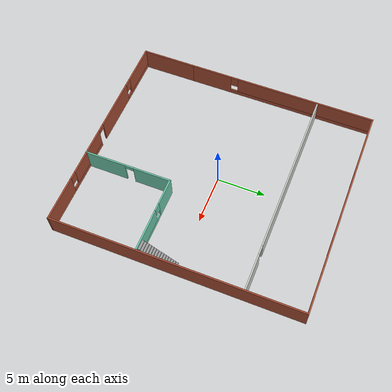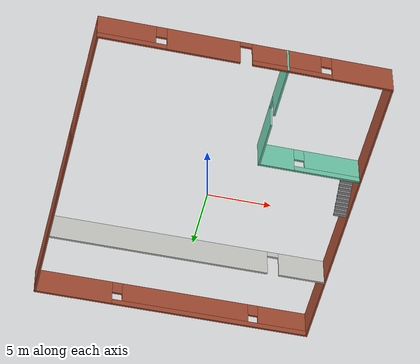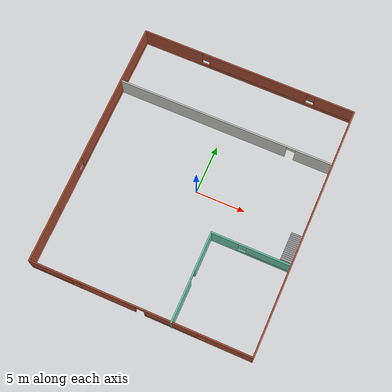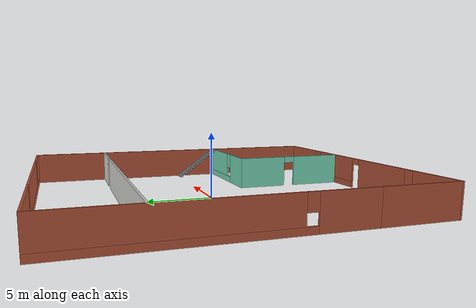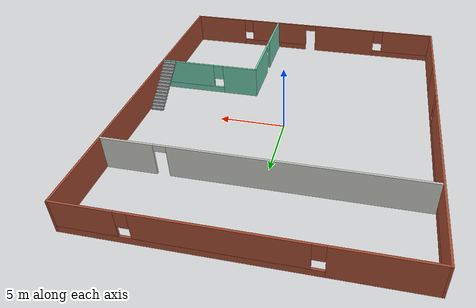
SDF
<?xml version='1.0'?>
<sdf version='1.6'>
  <model name='Building'>
    <link name='Stairs_0'>
      <pose frame=''>0 0 0 0 -0 0</pose>
      <self_collide>0</self_collide>
      <kinematic>0</kinematic>
      <visual name='Stairs_0_Visual_0'>
        <pose frame=''>10.3988 -0.214929 0.083333 0 -0 0</pose>
        <geometry>
          <box>
            <size>1 0.233333 0.166667</size>
          </box>
        </geometry>
        <material>
          <script>
            <uri>file://media/materials/scripts/gazebo.material</uri>
            <name>Gazebo/Grey</name>
          </script>
          <ambient>1 1 1 1</ambient>
          <shader type='pixel'/>
          <diffuse>0.7 0.7 0.7 1</diffuse>
          <specular>0.01 0.01 0.01 1</specular>
          <emissive>0 0 0 1</emissive>
        </material>
        <meta>
          <layer>0</layer>
        </meta>
        <transparency>0</transparency>
        <cast_shadows>1</cast_shadows>
      </visual>
      <visual name='Stairs_0_Visual_1'>
        <pose frame=''>10.3988 -0.448263 0.25 0 -0 0</pose>
        <geometry>
          <box>
            <size>1 0.233333 0.166667</size>
          </box>
        </geometry>
        <material>
          <script>
            <uri>file://media/materials/scripts/gazebo.material</uri>
            <name>Gazebo/Grey</name>
          </script>
          <ambient>1 1 1 1</ambient>
          <shader type='pixel'/>
          <diffuse>0.7 0.7 0.7 1</diffuse>
          <specular>0.01 0.01 0.01 1</specular>
          <emissive>0 0 0 1</emissive>
        </material>
        <meta>
          <layer>0</layer>
        </meta>
        <transparency>0</transparency>
        <cast_shadows>1</cast_shadows>
      </visual>
      <visual name='Stairs_0_Visual_2'>
        <pose frame=''>10.3988 -0.681596 0.416667 0 -0 0</pose>
        <geometry>
          <box>
            <size>1 0.233333 0.166667</size>
          </box>
        </geometry>
        <material>
          <script>
            <uri>file://media/materials/scripts/gazebo.material</uri>
            <name>Gazebo/Grey</name>
          </script>
          <ambient>1 1 1 1</ambient>
          <shader type='pixel'/>
          <diffuse>0.7 0.7 0.7 1</diffuse>
          <specular>0.01 0.01 0.01 1</specular>
          <emissive>0 0 0 1</emissive>
        </material>
        <meta>
          <layer>0</layer>
        </meta>
        <transparency>0</transparency>
        <cast_shadows>1</cast_shadows>
      </visual>
      <visual name='Stairs_0_Visual_3'>
        <pose frame=''>10.3988 -0.914929 0.583333 0 -0 0</pose>
        <geometry>
          <box>
            <size>1 0.233333 0.166667</size>
          </box>
        </geometry>
        <material>
          <script>
            <uri>file://media/materials/scripts/gazebo.material</uri>
            <name>Gazebo/Grey</name>
          </script>
          <ambient>1 1 1 1</ambient>
          <shader type='pixel'/>
          <diffuse>0.7 0.7 0.7 1</diffuse>
          <specular>0.01 0.01 0.01 1</specular>
          <emissive>0 0 0 1</emissive>
        </material>
        <meta>
          <layer>0</layer>
        </meta>
        <transparency>0</transparency>
        <cast_shadows>1</cast_shadows>
      </visual>
      <visual name='Stairs_0_Visual_4'>
        <pose frame=''>10.3988 -1.14826 0.75 0 -0 0</pose>
        <geometry>
          <box>
            <size>1 0.233333 0.166667</size>
          </box>
        </geometry>
        <material>
          <script>
            <uri>file://media/materials/scripts/gazebo.material</uri>
            <name>Gazebo/Grey</name>
          </script>
          <ambient>1 1 1 1</ambient>
          <shader type='pixel'/>
          <diffuse>0.7 0.7 0.7 1</diffuse>
          <specular>0.01 0.01 0.01 1</specular>
          <emissive>0 0 0 1</emissive>
        </material>
        <meta>
          <layer>0</layer>
        </meta>
        <transparency>0</transparency>
        <cast_shadows>1</cast_shadows>
      </visual>
      <visual name='Stairs_0_Visual_5'>
        <pose frame=''>10.3988 -1.3816 0.916667 0 -0 0</pose>
        <geometry>
          <box>
            <size>1 0.233333 0.166667</size>
          </box>
        </geometry>
        <material>
          <script>
            <uri>file://media/materials/scripts/gazebo.material</uri>
            <name>Gazebo/Grey</name>
          </script>
          <ambient>1 1 1 1</ambient>
          <shader type='pixel'/>
          <diffuse>0.7 0.7 0.7 1</diffuse>
          <specular>0.01 0.01 0.01 1</specular>
          <emissive>0 0 0 1</emissive>
        </material>
        <meta>
          <layer>0</layer>
        </meta>
        <transparency>0</transparency>
        <cast_shadows>1</cast_shadows>
      </visual>
      <visual name='Stairs_0_Visual_6'>
        <pose frame=''>10.3988 -1.61493 1.08333 0 -0 0</pose>
        <geometry>
          <box>
            <size>1 0.233333 0.166667</size>
          </box>
        </geometry>
        <material>
          <script>
            <uri>file://media/materials/scripts/gazebo.material</uri>
            <name>Gazebo/Grey</name>
          </script>
          <ambient>1 1 1 1</ambient>
          <shader type='pixel'/>
          <diffuse>0.7 0.7 0.7 1</diffuse>
          <specular>0.01 0.01 0.01 1</specular>
          <emissive>0 0 0 1</emissive>
        </material>
        <meta>
          <layer>0</layer>
        </meta>
        <transparency>0</transparency>
        <cast_shadows>1</cast_shadows>
      </visual>
      <visual name='Stairs_0_Visual_7'>
        <pose frame=''>10.3988 -1.84826 1.25 0 -0 0</pose>
        <geometry>
          <box>
            <size>1 0.233333 0.166667</size>
          </box>
        </geometry>
        <material>
          <script>
            <uri>file://media/materials/scripts/gazebo.material</uri>
            <name>Gazebo/Grey</name>
          </script>
          <ambient>1 1 1 1</ambient>
          <shader type='pixel'/>
          <diffuse>0.7 0.7 0.7 1</diffuse>
          <specular>0.01 0.01 0.01 1</specular>
          <emissive>0 0 0 1</emissive>
        </material>
        <meta>
          <layer>0</layer>
        </meta>
        <transparency>0</transparency>
        <cast_shadows>1</cast_shadows>
      </visual>
      <visual name='Stairs_0_Visual_8'>
        <pose frame=''>10.3988 -2.0816 1.41667 0 -0 0</pose>
        <geometry>
          <box>
            <size>1 0.233333 0.166667</size>
          </box>
        </geometry>
        <material>
          <script>
            <uri>file://media/materials/scripts/gazebo.material</uri>
            <name>Gazebo/Grey</name>
          </script>
          <ambient>1 1 1 1</ambient>
          <shader type='pixel'/>
          <diffuse>0.7 0.7 0.7 1</diffuse>
          <specular>0.01 0.01 0.01 1</specular>
          <emissive>0 0 0 1</emissive>
        </material>
        <meta>
          <layer>0</layer>
        </meta>
        <transparency>0</transparency>
        <cast_shadows>1</cast_shadows>
      </visual>
      <visual name='Stairs_0_Visual_9'>
        <pose frame=''>10.3988 -2.31493 1.58333 0 -0 0</pose>
        <geometry>
          <box>
            <size>1 0.233333 0.166667</size>
          </box>
        </geometry>
        <material>
          <script>
            <uri>file://media/materials/scripts/gazebo.material</uri>
            <name>Gazebo/Grey</name>
          </script>
          <ambient>1 1 1 1</ambient>
          <shader type='pixel'/>
          <diffuse>0.7 0.7 0.7 1</diffuse>
          <specular>0.01 0.01 0.01 1</specular>
          <emissive>0 0 0 1</emissive>
        </material>
        <meta>
          <layer>0</layer>
        </meta>
        <transparency>0</transparency>
        <cast_shadows>1</cast_shadows>
      </visual>
      <visual name='Stairs_0_Visual_10'>
        <pose frame=''>10.3988 -2.54826 1.75 0 -0 0</pose>
        <geometry>
          <box>
            <size>1 0.233333 0.166667</size>
          </box>
        </geometry>
        <material>
          <script>
            <uri>file://media/materials/scripts/gazebo.material</uri>
            <name>Gazebo/Grey</name>
          </script>
          <ambient>1 1 1 1</ambient>
          <shader type='pixel'/>
          <diffuse>0.7 0.7 0.7 1</diffuse>
          <specular>0.01 0.01 0.01 1</specular>
          <emissive>0 0 0 1</emissive>
        </material>
        <meta>
          <layer>0</layer>
        </meta>
        <transparency>0</transparency>
        <cast_shadows>1</cast_shadows>
      </visual>
      <visual name='Stairs_0_Visual_11'>
        <pose frame=''>10.3988 -2.7816 1.91667 0 -0 0</pose>
        <geometry>
          <box>
            <size>1 0.233333 0.166667</size>
          </box>
        </geometry>
        <material>
          <script>
            <uri>file://media/materials/scripts/gazebo.material</uri>
            <name>Gazebo/Grey</name>
          </script>
          <ambient>1 1 1 1</ambient>
          <shader type='pixel'/>
          <diffuse>0.7 0.7 0.7 1</diffuse>
          <specular>0.01 0.01 0.01 1</specular>
          <emissive>0 0 0 1</emissive>
        </material>
        <meta>
          <layer>0</layer>
        </meta>
        <transparency>0</transparency>
        <cast_shadows>1</cast_shadows>
      </visual>
      <visual name='Stairs_0_Visual_12'>
        <pose frame=''>10.3988 -3.01493 2.08333 0 -0 0</pose>
        <geometry>
          <box>
            <size>1 0.233333 0.166667</size>
          </box>
        </geometry>
        <material>
          <script>
            <uri>file://media/materials/scripts/gazebo.material</uri>
            <name>Gazebo/Grey</name>
          </script>
          <ambient>1 1 1 1</ambient>
          <shader type='pixel'/>
          <diffuse>0.7 0.7 0.7 1</diffuse>
          <specular>0.01 0.01 0.01 1</specular>
          <emissive>0 0 0 1</emissive>
        </material>
        <meta>
          <layer>0</layer>
        </meta>
        <transparency>0</transparency>
        <cast_shadows>1</cast_shadows>
      </visual>
      <visual name='Stairs_0_Visual_13'>
        <pose frame=''>10.3988 -3.24826 2.25 0 -0 0</pose>
        <geometry>
          <box>
            <size>1 0.233333 0.166667</size>
          </box>
        </geometry>
        <material>
          <script>
            <uri>file://media/materials/scripts/gazebo.material</uri>
            <name>Gazebo/Grey</name>
          </script>
          <ambient>1 1 1 1</ambient>
          <shader type='pixel'/>
          <diffuse>0.7 0.7 0.7 1</diffuse>
          <specular>0.01 0.01 0.01 1</specular>
          <emissive>0 0 0 1</emissive>
        </material>
        <meta>
          <layer>0</layer>
        </meta>
        <transparency>0</transparency>
        <cast_shadows>1</cast_shadows>
      </visual>
      <visual name='Stairs_0_Visual_14'>
        <pose frame=''>10.3988 -3.4816 2.41667 0 -0 0</pose>
        <geometry>
          <box>
            <size>1 0.233333 0.166667</size>
          </box>
        </geometry>
        <material>
          <script>
            <uri>file://media/materials/scripts/gazebo.material</uri>
            <name>Gazebo/Grey</name>
          </script>
          <ambient>1 1 1 1</ambient>
          <shader type='pixel'/>
          <diffuse>0.7 0.7 0.7 1</diffuse>
          <specular>0.01 0.01 0.01 1</specular>
          <emissive>0 0 0 1</emissive>
        </material>
        <meta>
          <layer>0</layer>
        </meta>
        <transparency>0</transparency>
        <cast_shadows>1</cast_shadows>
      </visual>
      <collision name='Stairs_0_Collision_0'>
        <laser_retro>0</laser_retro>
        <max_contacts>10</max_contacts>
        <pose frame=''>10.3988 -0.214929 0.083333 0 -0 0</pose>
        <geometry>
          <box>
            <size>1 0.233333 0.166667</size>
          </box>
        </geometry>
        <surface>
          <friction>
            <ode>
              <mu>1</mu>
              <mu2>1</mu2>
              <fdir1>0 0 0</fdir1>
              <slip1>0</slip1>
              <slip2>0</slip2>
            </ode>
            <torsional>
              <coefficient>1</coefficient>
              <patch_radius>0</patch_radius>
              <surface_radius>0</surface_radius>
              <use_patch_radius>1</use_patch_radius>
              <ode>
                <slip>0</slip>
              </ode>
            </torsional>
          </friction>
          <bounce>
            <restitution_coefficient>0</restitution_coefficient>
            <threshold>1e+06</threshold>
          </bounce>
          <contact>
            <collide_without_contact>0</collide_without_contact>
            <collide_without_contact_bitmask>1</collide_without_contact_bitmask>
            <collide_bitmask>1</collide_bitmask>
            <ode>
              <soft_cfm>0</soft_cfm>
              <soft_erp>0.2</soft_erp>
              <kp>1e+13</kp>
              <kd>1</kd>
              <max_vel>0.01</max_vel>
              <min_depth>0</min_depth>
            </ode>
            <bullet>
              <split_impulse>1</split_impulse>
              <split_impulse_penetration_threshold>-0.01</split_impulse_penetration_threshold>
              <soft_cfm>0</soft_cfm>
              <soft_erp>0.2</soft_erp>
              <kp>1e+13</kp>
              <kd>1</kd>
            </bullet>
          </contact>
        </surface>
      </collision>
      <collision name='Stairs_0_Collision_1'>
        <laser_retro>0</laser_retro>
        <max_contacts>10</max_contacts>
        <pose frame=''>10.3988 -0.448263 0.25 0 -0 0</pose>
        <geometry>
          <box>
            <size>1 0.233333 0.166667</size>
          </box>
        </geometry>
        <surface>
          <friction>
            <ode>
              <mu>1</mu>
              <mu2>1</mu2>
              <fdir1>0 0 0</fdir1>
              <slip1>0</slip1>
              <slip2>0</slip2>
            </ode>
            <torsional>
              <coefficient>1</coefficient>
              <patch_radius>0</patch_radius>
              <surface_radius>0</surface_radius>
              <use_patch_radius>1</use_patch_radius>
              <ode>
                <slip>0</slip>
              </ode>
            </torsional>
          </friction>
          <bounce>
            <restitution_coefficient>0</restitution_coefficient>
            <threshold>1e+06</threshold>
          </bounce>
          <contact>
            <collide_without_contact>0</collide_without_contact>
            <collide_without_contact_bitmask>1</collide_without_contact_bitmask>
            <collide_bitmask>1</collide_bitmask>
            <ode>
              <soft_cfm>0</soft_cfm>
              <soft_erp>0.2</soft_erp>
              <kp>1e+13</kp>
              <kd>1</kd>
              <max_vel>0.01</max_vel>
              <min_depth>0</min_depth>
            </ode>
            <bullet>
              <split_impulse>1</split_impulse>
              <split_impulse_penetration_threshold>-0.01</split_impulse_penetration_threshold>
              <soft_cfm>0</soft_cfm>
              <soft_erp>0.2</soft_erp>
              <kp>1e+13</kp>
              <kd>1</kd>
            </bullet>
          </contact>
        </surface>
      </collision>
      <collision name='Stairs_0_Collision_2'>
        <laser_retro>0</laser_retro>
        <max_contacts>10</max_contacts>
        <pose frame=''>10.3988 -0.681596 0.416667 0 -0 0</pose>
        <geometry>
          <box>
            <size>1 0.233333 0.166667</size>
          </box>
        </geometry>
        <surface>
          <friction>
            <ode>
              <mu>1</mu>
              <mu2>1</mu2>
              <fdir1>0 0 0</fdir1>
              <slip1>0</slip1>
              <slip2>0</slip2>
            </ode>
            <torsional>
              <coefficient>1</coefficient>
              <patch_radius>0</patch_radius>
              <surface_radius>0</surface_radius>
              <use_patch_radius>1</use_patch_radius>
              <ode>
                <slip>0</slip>
              </ode>
            </torsional>
          </friction>
          <bounce>
            <restitution_coefficient>0</restitution_coefficient>
            <threshold>1e+06</threshold>
          </bounce>
          <contact>
            <collide_without_contact>0</collide_without_contact>
            <collide_without_contact_bitmask>1</collide_without_contact_bitmask>
            <collide_bitmask>1</collide_bitmask>
            <ode>
              <soft_cfm>0</soft_cfm>
              <soft_erp>0.2</soft_erp>
              <kp>1e+13</kp>
              <kd>1</kd>
              <max_vel>0.01</max_vel>
              <min_depth>0</min_depth>
            </ode>
            <bullet>
              <split_impulse>1</split_impulse>
              <split_impulse_penetration_threshold>-0.01</split_impulse_penetration_threshold>
              <soft_cfm>0</soft_cfm>
              <soft_erp>0.2</soft_erp>
              <kp>1e+13</kp>
              <kd>1</kd>
            </bullet>
          </contact>
        </surface>
      </collision>
      <collision name='Stairs_0_Collision_8'>
        <laser_retro>0</laser_retro>
        <max_contacts>10</max_contacts>
        <pose frame=''>10.3988 -2.0816 1.41667 0 -0 0</pose>
        <geometry>
          <box>
            <size>1 0.233333 0.166667</size>
          </box>
        </geometry>
        <surface>
          <friction>
            <ode>
              <mu>1</mu>
              <mu2>1</mu2>
              <fdir1>0 0 0</fdir1>
              <slip1>0</slip1>
              <slip2>0</slip2>
            </ode>
            <torsional>
              <coefficient>1</coefficient>
              <patch_radius>0</patch_radius>
              <surface_radius>0</surface_radius>
              <use_patch_radius>1</use_patch_radius>
              <ode>
                <slip>0</slip>
              </ode>
            </torsional>
          </friction>
          <bounce>
            <restitution_coefficient>0</restitution_coefficient>
            <threshold>1e+06</threshold>
          </bounce>
          <contact>
            <collide_without_contact>0</collide_without_contact>
            <collide_without_contact_bitmask>1</collide_without_contact_bitmask>
            <collide_bitmask>1</collide_bitmask>
            <ode>
              <soft_cfm>0</soft_cfm>
              <soft_erp>0.2</soft_erp>
              <kp>1e+13</kp>
              <kd>1</kd>
              <max_vel>0.01</max_vel>
              <min_depth>0</min_depth>
            </ode>
            <bullet>
              <split_impulse>1</split_impulse>
              <split_impulse_penetration_threshold>-0.01</split_impulse_penetration_threshold>
              <soft_cfm>0</soft_cfm>
              <soft_erp>0.2</soft_erp>
              <kp>1e+13</kp>
              <kd>1</kd>
            </bullet>
          </contact>
        </surface>
      </collision>
      <collision name='Stairs_0_Collision_3'>
        <laser_retro>0</laser_retro>
        <max_contacts>10</max_contacts>
        <pose frame=''>10.3988 -0.914929 0.583333 0 -0 0</pose>
        <geometry>
          <box>
            <size>1 0.233333 0.166667</size>
          </box>
        </geometry>
        <surface>
          <friction>
            <ode>
              <mu>1</mu>
              <mu2>1</mu2>
              <fdir1>0 0 0</fdir1>
              <slip1>0</slip1>
              <slip2>0</slip2>
            </ode>
            <torsional>
              <coefficient>1</coefficient>
              <patch_radius>0</patch_radius>
              <surface_radius>0</surface_radius>
              <use_patch_radius>1</use_patch_radius>
              <ode>
                <slip>0</slip>
              </ode>
            </torsional>
          </friction>
          <bounce>
            <restitution_coefficient>0</restitution_coefficient>
            <threshold>1e+06</threshold>
          </bounce>
          <contact>
            <collide_without_contact>0</collide_without_contact>
            <collide_without_contact_bitmask>1</collide_without_contact_bitmask>
            <collide_bitmask>1</collide_bitmask>
            <ode>
              <soft_cfm>0</soft_cfm>
              <soft_erp>0.2</soft_erp>
              <kp>1e+13</kp>
              <kd>1</kd>
              <max_vel>0.01</max_vel>
              <min_depth>0</min_depth>
            </ode>
            <bullet>
              <split_impulse>1</split_impulse>
              <split_impulse_penetration_threshold>-0.01</split_impulse_penetration_threshold>
              <soft_cfm>0</soft_cfm>
              <soft_erp>0.2</soft_erp>
              <kp>1e+13</kp>
              <kd>1</kd>
            </bullet>
          </contact>
        </surface>
      </collision>
      <collision name='Stairs_0_Collision_6'>
        <laser_retro>0</laser_retro>
        <max_contacts>10</max_contacts>
        <pose frame=''>10.3988 -1.61493 1.08333 0 -0 0</pose>
        <geometry>
          <box>
            <size>1 0.233333 0.166667</size>
          </box>
        </geometry>
        <surface>
          <friction>
            <ode>
              <mu>1</mu>
              <mu2>1</mu2>
              <fdir1>0 0 0</fdir1>
              <slip1>0</slip1>
              <slip2>0</slip2>
            </ode>
            <torsional>
              <coefficient>1</coefficient>
              <patch_radius>0</patch_radius>
              <surface_radius>0</surface_radius>
              <use_patch_radius>1</use_patch_radius>
              <ode>
                <slip>0</slip>
              </ode>
            </torsional>
          </friction>
          <bounce>
            <restitution_coefficient>0</restitution_coefficient>
            <threshold>1e+06</threshold>
          </bounce>
          <contact>
            <collide_without_contact>0</collide_without_contact>
            <collide_without_contact_bitmask>1</collide_without_contact_bitmask>
            <collide_bitmask>1</collide_bitmask>
            <ode>
              <soft_cfm>0</soft_cfm>
              <soft_erp>0.2</soft_erp>
              <kp>1e+13</kp>
              <kd>1</kd>
              <max_vel>0.01</max_vel>
              <min_depth>0</min_depth>
            </ode>
            <bullet>
              <split_impulse>1</split_impulse>
              <split_impulse_penetration_threshold>-0.01</split_impulse_penetration_threshold>
              <soft_cfm>0</soft_cfm>
              <soft_erp>0.2</soft_erp>
              <kp>1e+13</kp>
              <kd>1</kd>
            </bullet>
          </contact>
        </surface>
      </collision>
      <collision name='Stairs_0_Collision_4'>
        <laser_retro>0</laser_retro>
        <max_contacts>10</max_contacts>
        <pose frame=''>10.3988 -1.14826 0.75 0 -0 0</pose>
        <geometry>
          <box>
            <size>1 0.233333 0.166667</size>
          </box>
        </geometry>
        <surface>
          <friction>
            <ode>
              <mu>1</mu>
              <mu2>1</mu2>
              <fdir1>0 0 0</fdir1>
              <slip1>0</slip1>
              <slip2>0</slip2>
            </ode>
            <torsional>
              <coefficient>1</coefficient>
              <patch_radius>0</patch_radius>
              <surface_radius>0</surface_radius>
              <use_patch_radius>1</use_patch_radius>
              <ode>
                <slip>0</slip>
              </ode>
            </torsional>
          </friction>
          <bounce>
            <restitution_coefficient>0</restitution_coefficient>
            <threshold>1e+06</threshold>
          </bounce>
          <contact>
            <collide_without_contact>0</collide_without_contact>
            <collide_without_contact_bitmask>1</collide_without_contact_bitmask>
            <collide_bitmask>1</collide_bitmask>
            <ode>
              <soft_cfm>0</soft_cfm>
              <soft_erp>0.2</soft_erp>
              <kp>1e+13</kp>
              <kd>1</kd>
              <max_vel>0.01</max_vel>
              <min_depth>0</min_depth>
            </ode>
            <bullet>
              <split_impulse>1</split_impulse>
              <split_impulse_penetration_threshold>-0.01</split_impulse_penetration_threshold>
              <soft_cfm>0</soft_cfm>
              <soft_erp>0.2</soft_erp>
              <kp>1e+13</kp>
              <kd>1</kd>
            </bullet>
          </contact>
        </surface>
      </collision>
      <collision name='Stairs_0_Collision_5'>
        <laser_retro>0</laser_retro>
        <max_contacts>10</max_contacts>
        <pose frame=''>10.3988 -1.3816 0.916667 0 -0 0</pose>
        <geometry>
          <box>
            <size>1 0.233333 0.166667</size>
          </box>
        </geometry>
        <surface>
          <friction>
            <ode>
              <mu>1</mu>
              <mu2>1</mu2>
              <fdir1>0 0 0</fdir1>
              <slip1>0</slip1>
              <slip2>0</slip2>
            </ode>
            <torsional>
              <coefficient>1</coefficient>
              <patch_radius>0</patch_radius>
              <surface_radius>0</surface_radius>
              <use_patch_radius>1</use_patch_radius>
              <ode>
                <slip>0</slip>
              </ode>
            </torsional>
          </friction>
          <bounce>
            <restitution_coefficient>0</restitution_coefficient>
            <threshold>1e+06</threshold>
          </bounce>
          <contact>
            <collide_without_contact>0</collide_without_contact>
            <collide_without_contact_bitmask>1</collide_without_contact_bitmask>
            <collide_bitmask>1</collide_bitmask>
            <ode>
              <soft_cfm>0</soft_cfm>
              <soft_erp>0.2</soft_erp>
              <kp>1e+13</kp>
              <kd>1</kd>
              <max_vel>0.01</max_vel>
              <min_depth>0</min_depth>
            </ode>
            <bullet>
              <split_impulse>1</split_impulse>
              <split_impulse_penetration_threshold>-0.01</split_impulse_penetration_threshold>
              <soft_cfm>0</soft_cfm>
              <soft_erp>0.2</soft_erp>
              <kp>1e+13</kp>
              <kd>1</kd>
            </bullet>
          </contact>
        </surface>
      </collision>
      <collision name='Stairs_0_Collision_7'>
        <laser_retro>0</laser_retro>
        <max_contacts>10</max_contacts>
        <pose frame=''>10.3988 -1.84826 1.25 0 -0 0</pose>
        <geometry>
          <box>
            <size>1 0.233333 0.166667</size>
          </box>
        </geometry>
        <surface>
          <friction>
            <ode>
              <mu>1</mu>
              <mu2>1</mu2>
              <fdir1>0 0 0</fdir1>
              <slip1>0</slip1>
              <slip2>0</slip2>
            </ode>
            <torsional>
              <coefficient>1</coefficient>
              <patch_radius>0</patch_radius>
              <surface_radius>0</surface_radius>
              <use_patch_radius>1</use_patch_radius>
              <ode>
                <slip>0</slip>
              </ode>
            </torsional>
          </friction>
          <bounce>
            <restitution_coefficient>0</restitution_coefficient>
            <threshold>1e+06</threshold>
          </bounce>
          <contact>
            <collide_without_contact>0</collide_without_contact>
            <collide_without_contact_bitmask>1</collide_without_contact_bitmask>
            <collide_bitmask>1</collide_bitmask>
            <ode>
              <soft_cfm>0</soft_cfm>
              <soft_erp>0.2</soft_erp>
              <kp>1e+13</kp>
              <kd>1</kd>
              <max_vel>0.01</max_vel>
              <min_depth>0</min_depth>
            </ode>
            <bullet>
              <split_impulse>1</split_impulse>
              <split_impulse_penetration_threshold>-0.01</split_impulse_penetration_threshold>
              <soft_cfm>0</soft_cfm>
              <soft_erp>0.2</soft_erp>
              <kp>1e+13</kp>
              <kd>1</kd>
            </bullet>
          </contact>
        </surface>
      </collision>
      <collision name='Stairs_0_Collision_9'>
        <laser_retro>0</laser_retro>
        <max_contacts>10</max_contacts>
        <pose frame=''>10.3988 -2.31493 1.58333 0 -0 0</pose>
        <geometry>
          <box>
            <size>1 0.233333 0.166667</size>
          </box>
        </geometry>
        <surface>
          <friction>
            <ode>
              <mu>1</mu>
              <mu2>1</mu2>
              <fdir1>0 0 0</fdir1>
              <slip1>0</slip1>
              <slip2>0</slip2>
            </ode>
            <torsional>
              <coefficient>1</coefficient>
              <patch_radius>0</patch_radius>
              <surface_radius>0</surface_radius>
              <use_patch_radius>1</use_patch_radius>
              <ode>
                <slip>0</slip>
              </ode>
            </torsional>
          </friction>
          <bounce>
            <restitution_coefficient>0</restitution_coefficient>
            <threshold>1e+06</threshold>
          </bounce>
          <contact>
            <collide_without_contact>0</collide_without_contact>
            <collide_without_contact_bitmask>1</collide_without_contact_bitmask>
            <collide_bitmask>1</collide_bitmask>
            <ode>
              <soft_cfm>0</soft_cfm>
              <soft_erp>0.2</soft_erp>
              <kp>1e+13</kp>
              <kd>1</kd>
              <max_vel>0.01</max_vel>
              <min_depth>0</min_depth>
            </ode>
            <bullet>
              <split_impulse>1</split_impulse>
              <split_impulse_penetration_threshold>-0.01</split_impulse_penetration_threshold>
              <soft_cfm>0</soft_cfm>
              <soft_erp>0.2</soft_erp>
              <kp>1e+13</kp>
              <kd>1</kd>
            </bullet>
          </contact>
        </surface>
      </collision>
      <collision name='Stairs_0_Collision_10'>
        <laser_retro>0</laser_retro>
        <max_contacts>10</max_contacts>
        <pose frame=''>10.3988 -2.54826 1.75 0 -0 0</pose>
        <geometry>
          <box>
            <size>1 0.233333 0.166667</size>
          </box>
        </geometry>
        <surface>
          <friction>
            <ode>
              <mu>1</mu>
              <mu2>1</mu2>
              <fdir1>0 0 0</fdir1>
              <slip1>0</slip1>
              <slip2>0</slip2>
            </ode>
            <torsional>
              <coefficient>1</coefficient>
              <patch_radius>0</patch_radius>
              <surface_radius>0</surface_radius>
              <use_patch_radius>1</use_patch_radius>
              <ode>
                <slip>0</slip>
              </ode>
            </torsional>
          </friction>
          <bounce>
            <restitution_coefficient>0</restitution_coefficient>
            <threshold>1e+06</threshold>
          </bounce>
          <contact>
            <collide_without_contact>0</collide_without_contact>
            <collide_without_contact_bitmask>1</collide_without_contact_bitmask>
            <collide_bitmask>1</collide_bitmask>
            <ode>
              <soft_cfm>0</soft_cfm>
              <soft_erp>0.2</soft_erp>
              <kp>1e+13</kp>
              <kd>1</kd>
              <max_vel>0.01</max_vel>
              <min_depth>0</min_depth>
            </ode>
            <bullet>
              <split_impulse>1</split_impulse>
              <split_impulse_penetration_threshold>-0.01</split_impulse_penetration_threshold>
              <soft_cfm>0</soft_cfm>
              <soft_erp>0.2</soft_erp>
              <kp>1e+13</kp>
              <kd>1</kd>
            </bullet>
          </contact>
        </surface>
      </collision>
      <collision name='Stairs_0_Collision_14'>
        <laser_retro>0</laser_retro>
        <max_contacts>10</max_contacts>
        <pose frame=''>10.3988 -3.4816 2.41667 0 -0 0</pose>
        <geometry>
          <box>
            <size>1 0.233333 0.166667</size>
          </box>
        </geometry>
        <surface>
          <friction>
            <ode>
              <mu>1</mu>
              <mu2>1</mu2>
              <fdir1>0 0 0</fdir1>
              <slip1>0</slip1>
              <slip2>0</slip2>
            </ode>
            <torsional>
              <coefficient>1</coefficient>
              <patch_radius>0</patch_radius>
              <surface_radius>0</surface_radius>
              <use_patch_radius>1</use_patch_radius>
              <ode>
                <slip>0</slip>
              </ode>
            </torsional>
          </friction>
          <bounce>
            <restitution_coefficient>0</restitution_coefficient>
            <threshold>1e+06</threshold>
          </bounce>
          <contact>
            <collide_without_contact>0</collide_without_contact>
            <collide_without_contact_bitmask>1</collide_without_contact_bitmask>
            <collide_bitmask>1</collide_bitmask>
            <ode>
              <soft_cfm>0</soft_cfm>
              <soft_erp>0.2</soft_erp>
              <kp>1e+13</kp>
              <kd>1</kd>
              <max_vel>0.01</max_vel>
              <min_depth>0</min_depth>
            </ode>
            <bullet>
              <split_impulse>1</split_impulse>
              <split_impulse_penetration_threshold>-0.01</split_impulse_penetration_threshold>
              <soft_cfm>0</soft_cfm>
              <soft_erp>0.2</soft_erp>
              <kp>1e+13</kp>
              <kd>1</kd>
            </bullet>
          </contact>
        </surface>
      </collision>
      <collision name='Stairs_0_Collision_11'>
        <laser_retro>0</laser_retro>
        <max_contacts>10</max_contacts>
        <pose frame=''>10.3988 -2.7816 1.91667 0 -0 0</pose>
        <geometry>
          <box>
            <size>1 0.233333 0.166667</size>
          </box>
        </geometry>
        <surface>
          <friction>
            <ode>
              <mu>1</mu>
              <mu2>1</mu2>
              <fdir1>0 0 0</fdir1>
              <slip1>0</slip1>
              <slip2>0</slip2>
            </ode>
            <torsional>
              <coefficient>1</coefficient>
              <patch_radius>0</patch_radius>
              <surface_radius>0</surface_radius>
              <use_patch_radius>1</use_patch_radius>
              <ode>
                <slip>0</slip>
              </ode>
            </torsional>
          </friction>
          <bounce>
            <restitution_coefficient>0</restitution_coefficient>
            <threshold>1e+06</threshold>
          </bounce>
          <contact>
            <collide_without_contact>0</collide_without_contact>
            <collide_without_contact_bitmask>1</collide_without_contact_bitmask>
            <collide_bitmask>1</collide_bitmask>
            <ode>
              <soft_cfm>0</soft_cfm>
              <soft_erp>0.2</soft_erp>
              <kp>1e+13</kp>
              <kd>1</kd>
              <max_vel>0.01</max_vel>
              <min_depth>0</min_depth>
            </ode>
            <bullet>
              <split_impulse>1</split_impulse>
              <split_impulse_penetration_threshold>-0.01</split_impulse_penetration_threshold>
              <soft_cfm>0</soft_cfm>
              <soft_erp>0.2</soft_erp>
              <kp>1e+13</kp>
              <kd>1</kd>
            </bullet>
          </contact>
        </surface>
      </collision>
      <collision name='Stairs_0_Collision_12'>
        <laser_retro>0</laser_retro>
        <max_contacts>10</max_contacts>
        <pose frame=''>10.3988 -3.01493 2.08333 0 -0 0</pose>
        <geometry>
          <box>
            <size>1 0.233333 0.166667</size>
          </box>
        </geometry>
        <surface>
          <friction>
            <ode>
              <mu>1</mu>
              <mu2>1</mu2>
              <fdir1>0 0 0</fdir1>
              <slip1>0</slip1>
              <slip2>0</slip2>
            </ode>
            <torsional>
              <coefficient>1</coefficient>
              <patch_radius>0</patch_radius>
              <surface_radius>0</surface_radius>
              <use_patch_radius>1</use_patch_radius>
              <ode>
                <slip>0</slip>
              </ode>
            </torsional>
          </friction>
          <bounce>
            <restitution_coefficient>0</restitution_coefficient>
            <threshold>1e+06</threshold>
          </bounce>
          <contact>
            <collide_without_contact>0</collide_without_contact>
            <collide_without_contact_bitmask>1</collide_without_contact_bitmask>
            <collide_bitmask>1</collide_bitmask>
            <ode>
              <soft_cfm>0</soft_cfm>
              <soft_erp>0.2</soft_erp>
              <kp>1e+13</kp>
              <kd>1</kd>
              <max_vel>0.01</max_vel>
              <min_depth>0</min_depth>
            </ode>
            <bullet>
              <split_impulse>1</split_impulse>
              <split_impulse_penetration_threshold>-0.01</split_impulse_penetration_threshold>
              <soft_cfm>0</soft_cfm>
              <soft_erp>0.2</soft_erp>
              <kp>1e+13</kp>
              <kd>1</kd>
            </bullet>
          </contact>
        </surface>
      </collision>
      <collision name='Stairs_0_Collision_13'>
        <laser_retro>0</laser_retro>
        <max_contacts>10</max_contacts>
        <pose frame=''>10.3988 -3.24826 2.25 0 -0 0</pose>
        <geometry>
          <box>
            <size>1 0.233333 0.166667</size>
          </box>
        </geometry>
        <surface>
          <friction>
            <ode>
              <mu>1</mu>
              <mu2>1</mu2>
              <fdir1>0 0 0</fdir1>
              <slip1>0</slip1>
              <slip2>0</slip2>
            </ode>
            <torsional>
              <coefficient>1</coefficient>
              <patch_radius>0</patch_radius>
              <surface_radius>0</surface_radius>
              <use_patch_radius>1</use_patch_radius>
              <ode>
                <slip>0</slip>
              </ode>
            </torsional>
          </friction>
          <bounce>
            <restitution_coefficient>0</restitution_coefficient>
            <threshold>1e+06</threshold>
          </bounce>
          <contact>
            <collide_without_contact>0</collide_without_contact>
            <collide_without_contact_bitmask>1</collide_without_contact_bitmask>
            <collide_bitmask>1</collide_bitmask>
            <ode>
              <soft_cfm>0</soft_cfm>
              <soft_erp>0.2</soft_erp>
              <kp>1e+13</kp>
              <kd>1</kd>
              <max_vel>0.01</max_vel>
              <min_depth>0</min_depth>
            </ode>
            <bullet>
              <split_impulse>1</split_impulse>
              <split_impulse_penetration_threshold>-0.01</split_impulse_penetration_threshold>
              <soft_cfm>0</soft_cfm>
              <soft_erp>0.2</soft_erp>
              <kp>1e+13</kp>
              <kd>1</kd>
            </bullet>
          </contact>
        </surface>
      </collision>
    </link>
    <link name='Wall_0'>
      <pose frame=''>-11.05 2.85254 0 0 -0 1.5708</pose>
      <self_collide>0</self_collide>
      <kinematic>0</kinematic>
      <visual name='Wall_0_Visual_0'>
        <pose frame=''>-7.80775 0 1.25 0 -0 0</pose>
        <geometry>
          <box>
            <size>4.3845 0.15 2.5</size>
          </box>
        </geometry>
        <material>
          <script>
            <uri>file://media/materials/scripts/gazebo.material</uri>
            <name>Gazebo/Bricks</name>
          </script>
          <ambient>1 1 1 1</ambient>
          <shader type='pixel'/>
          <diffuse>1 1 1 1</diffuse>
          <specular>0.2 0.2 0.2 1</specular>
          <emissive>0 0 0 1</emissive>
        </material>
        <meta>
          <layer>0</layer>
        </meta>
        <transparency>0</transparency>
        <cast_shadows>1</cast_shadows>
      </visual>
      <visual name='Wall_0_Visual_1'>
        <pose frame=''>2.19225 0 0.25 0 -0 0</pose>
        <geometry>
          <box>
            <size>15.6155 0.15 0.5</size>
          </box>
        </geometry>
        <material>
          <script>
            <uri>file://media/materials/scripts/gazebo.material</uri>
            <name>Gazebo/Bricks</name>
          </script>
          <ambient>1 1 1 1</ambient>
          <shader type='pixel'/>
          <diffuse>1 1 1 1</diffuse>
          <specular>0.2 0.2 0.2 1</specular>
          <emissive>0 0 0 1</emissive>
        </material>
        <meta>
          <layer>0</layer>
        </meta>
        <transparency>0</transparency>
        <cast_shadows>1</cast_shadows>
      </visual>
      <visual name='Wall_0_Visual_2'>
        <pose frame=''>2.59225 0 1.5 0 -0 0</pose>
        <geometry>
          <box>
            <size>14.8155 0.15 2</size>
          </box>
        </geometry>
        <material>
          <script>
            <uri>file://media/materials/scripts/gazebo.material</uri>
            <name>Gazebo/Bricks</name>
          </script>
          <ambient>1 1 1 1</ambient>
          <shader type='pixel'/>
          <diffuse>1 1 1 1</diffuse>
          <specular>0.2 0.2 0.2 1</specular>
          <emissive>0 0 0 1</emissive>
        </material>
        <meta>
          <layer>0</layer>
        </meta>
        <transparency>0</transparency>
        <cast_shadows>1</cast_shadows>
      </visual>
      <visual name='Wall_0_Visual_3'>
        <pose frame=''>-5.2155 0 1.9 0 -0 0</pose>
        <geometry>
          <box>
            <size>0.8 0.15 1.2</size>
          </box>
        </geometry>
        <material>
          <script>
            <uri>file://media/materials/scripts/gazebo.material</uri>
            <name>Gazebo/Bricks</name>
          </script>
          <ambient>1 1 1 1</ambient>
          <shader type='pixel'/>
          <diffuse>1 1 1 1</diffuse>
          <specular>0.2 0.2 0.2 1</specular>
          <emissive>0 0 0 1</emissive>
        </material>
        <meta>
          <layer>0</layer>
        </meta>
        <transparency>0</transparency>
        <cast_shadows>1</cast_shadows>
      </visual>
      <collision name='Wall_0_Collision_0'>
        <laser_retro>0</laser_retro>
        <max_contacts>10</max_contacts>
        <pose frame=''>-7.80775 0 1.25 0 -0 0</pose>
        <geometry>
          <box>
            <size>4.3845 0.15 2.5</size>
          </box>
        </geometry>
        <surface>
          <friction>
            <ode>
              <mu>1</mu>
              <mu2>1</mu2>
              <fdir1>0 0 0</fdir1>
              <slip1>0</slip1>
              <slip2>0</slip2>
            </ode>
            <torsional>
              <coefficient>1</coefficient>
              <patch_radius>0</patch_radius>
              <surface_radius>0</surface_radius>
              <use_patch_radius>1</use_patch_radius>
              <ode>
                <slip>0</slip>
              </ode>
            </torsional>
          </friction>
          <bounce>
            <restitution_coefficient>0</restitution_coefficient>
            <threshold>1e+06</threshold>
          </bounce>
          <contact>
            <collide_without_contact>0</collide_without_contact>
            <collide_without_contact_bitmask>1</collide_without_contact_bitmask>
            <collide_bitmask>1</collide_bitmask>
            <ode>
              <soft_cfm>0</soft_cfm>
              <soft_erp>0.2</soft_erp>
              <kp>1e+13</kp>
              <kd>1</kd>
              <max_vel>0.01</max_vel>
              <min_depth>0</min_depth>
            </ode>
            <bullet>
              <split_impulse>1</split_impulse>
              <split_impulse_penetration_threshold>-0.01</split_impulse_penetration_threshold>
              <soft_cfm>0</soft_cfm>
              <soft_erp>0.2</soft_erp>
              <kp>1e+13</kp>
              <kd>1</kd>
            </bullet>
          </contact>
        </surface>
      </collision>
      <collision name='Wall_0_Collision_1'>
        <laser_retro>0</laser_retro>
        <max_contacts>10</max_contacts>
        <pose frame=''>2.19225 0 0.25 0 -0 0</pose>
        <geometry>
          <box>
            <size>15.6155 0.15 0.5</size>
          </box>
        </geometry>
        <surface>
          <friction>
            <ode>
              <mu>1</mu>
              <mu2>1</mu2>
              <fdir1>0 0 0</fdir1>
              <slip1>0</slip1>
              <slip2>0</slip2>
            </ode>
            <torsional>
              <coefficient>1</coefficient>
              <patch_radius>0</patch_radius>
              <surface_radius>0</surface_radius>
              <use_patch_radius>1</use_patch_radius>
              <ode>
                <slip>0</slip>
              </ode>
            </torsional>
          </friction>
          <bounce>
            <restitution_coefficient>0</restitution_coefficient>
            <threshold>1e+06</threshold>
          </bounce>
          <contact>
            <collide_without_contact>0</collide_without_contact>
            <collide_without_contact_bitmask>1</collide_without_contact_bitmask>
            <collide_bitmask>1</collide_bitmask>
            <ode>
              <soft_cfm>0</soft_cfm>
              <soft_erp>0.2</soft_erp>
              <kp>1e+13</kp>
              <kd>1</kd>
              <max_vel>0.01</max_vel>
              <min_depth>0</min_depth>
            </ode>
            <bullet>
              <split_impulse>1</split_impulse>
              <split_impulse_penetration_threshold>-0.01</split_impulse_penetration_threshold>
              <soft_cfm>0</soft_cfm>
              <soft_erp>0.2</soft_erp>
              <kp>1e+13</kp>
              <kd>1</kd>
            </bullet>
          </contact>
        </surface>
      </collision>
      <collision name='Wall_0_Collision_2'>
        <laser_retro>0</laser_retro>
        <max_contacts>10</max_contacts>
        <pose frame=''>2.59225 0 1.5 0 -0 0</pose>
        <geometry>
          <box>
            <size>14.8155 0.15 2</size>
          </box>
        </geometry>
        <surface>
          <friction>
            <ode>
              <mu>1</mu>
              <mu2>1</mu2>
              <fdir1>0 0 0</fdir1>
              <slip1>0</slip1>
              <slip2>0</slip2>
            </ode>
            <torsional>
              <coefficient>1</coefficient>
              <patch_radius>0</patch_radius>
              <surface_radius>0</surface_radius>
              <use_patch_radius>1</use_patch_radius>
              <ode>
                <slip>0</slip>
              </ode>
            </torsional>
          </friction>
          <bounce>
            <restitution_coefficient>0</restitution_coefficient>
            <threshold>1e+06</threshold>
          </bounce>
          <contact>
            <collide_without_contact>0</collide_without_contact>
            <collide_without_contact_bitmask>1</collide_without_contact_bitmask>
            <collide_bitmask>1</collide_bitmask>
            <ode>
              <soft_cfm>0</soft_cfm>
              <soft_erp>0.2</soft_erp>
              <kp>1e+13</kp>
              <kd>1</kd>
              <max_vel>0.01</max_vel>
              <min_depth>0</min_depth>
            </ode>
            <bullet>
              <split_impulse>1</split_impulse>
              <split_impulse_penetration_threshold>-0.01</split_impulse_penetration_threshold>
              <soft_cfm>0</soft_cfm>
              <soft_erp>0.2</soft_erp>
              <kp>1e+13</kp>
              <kd>1</kd>
            </bullet>
          </contact>
        </surface>
      </collision>
      <collision name='Wall_0_Collision_3'>
        <laser_retro>0</laser_retro>
        <max_contacts>10</max_contacts>
        <pose frame=''>-5.2155 0 1.9 0 -0 0</pose>
        <geometry>
          <box>
            <size>0.8 0.15 1.2</size>
          </box>
        </geometry>
        <surface>
          <friction>
            <ode>
              <mu>1</mu>
              <mu2>1</mu2>
              <fdir1>0 0 0</fdir1>
              <slip1>0</slip1>
              <slip2>0</slip2>
            </ode>
            <torsional>
              <coefficient>1</coefficient>
              <patch_radius>0</patch_radius>
              <surface_radius>0</surface_radius>
              <use_patch_radius>1</use_patch_radius>
              <ode>
                <slip>0</slip>
              </ode>
            </torsional>
          </friction>
          <bounce>
            <restitution_coefficient>0</restitution_coefficient>
            <threshold>1e+06</threshold>
          </bounce>
          <contact>
            <collide_without_contact>0</collide_without_contact>
            <collide_without_contact_bitmask>1</collide_without_contact_bitmask>
            <collide_bitmask>1</collide_bitmask>
            <ode>
              <soft_cfm>0</soft_cfm>
              <soft_erp>0.2</soft_erp>
              <kp>1e+13</kp>
              <kd>1</kd>
              <max_vel>0.01</max_vel>
              <min_depth>0</min_depth>
            </ode>
            <bullet>
              <split_impulse>1</split_impulse>
              <split_impulse_penetration_threshold>-0.01</split_impulse_penetration_threshold>
              <soft_cfm>0</soft_cfm>
              <soft_erp>0.2</soft_erp>
              <kp>1e+13</kp>
              <kd>1</kd>
            </bullet>
          </contact>
        </surface>
      </collision>
    </link>
    <link name='Wall_16'>
      <pose frame=''>3.13852 -8.31175 0 0 -0 1.5708</pose>
      <self_collide>0</self_collide>
      <kinematic>0</kinematic>
      <visual name='Wall_16_Visual_0'>
        <pose frame=''>-2.44368 0 1.25 0 -0 0</pose>
        <geometry>
          <box>
            <size>4.36265 0.15 2.5</size>
          </box>
        </geometry>
        <material>
          <script>
            <uri>file://media/materials/scripts/gazebo.material</uri>
            <name>Gazebo/Grey</name>
          </script>
          <ambient>0.435294 0.796078 0.67451 1</ambient>
          <shader type='pixel'/>
          <diffuse>0.7 0.7 0.7 1</diffuse>
          <specular>0.01 0.01 0.01 1</specular>
          <emissive>0 0 0 1</emissive>
        </material>
        <meta>
          <layer>0</layer>
        </meta>
        <transparency>0</transparency>
        <cast_shadows>1</cast_shadows>
      </visual>
      <visual name='Wall_16_Visual_1'>
        <pose frame=''>2.63132 0 1.25 0 -0 0</pose>
        <geometry>
          <box>
            <size>3.98735 0.15 2.5</size>
          </box>
        </geometry>
        <material>
          <script>
            <uri>file://media/materials/scripts/gazebo.material</uri>
            <name>Gazebo/Grey</name>
          </script>
          <ambient>0.435294 0.796078 0.67451 1</ambient>
          <shader type='pixel'/>
          <diffuse>0.7 0.7 0.7 1</diffuse>
          <specular>0.01 0.01 0.01 1</specular>
          <emissive>0 0 0 1</emissive>
        </material>
        <meta>
          <layer>0</layer>
        </meta>
        <transparency>0</transparency>
        <cast_shadows>1</cast_shadows>
      </visual>
      <visual name='Wall_16_Visual_2'>
        <pose frame=''>0.187646 0 2.25 0 -0 0</pose>
        <geometry>
          <box>
            <size>0.9 0.15 0.5</size>
          </box>
        </geometry>
        <material>
          <script>
            <uri>file://media/materials/scripts/gazebo.material</uri>
            <name>Gazebo/Grey</name>
          </script>
          <ambient>0.435294 0.796078 0.67451 1</ambient>
          <shader type='pixel'/>
          <diffuse>0.7 0.7 0.7 1</diffuse>
          <specular>0.01 0.01 0.01 1</specular>
          <emissive>0 0 0 1</emissive>
        </material>
        <meta>
          <layer>0</layer>
        </meta>
        <transparency>0</transparency>
        <cast_shadows>1</cast_shadows>
      </visual>
      <collision name='Wall_16_Collision_0'>
        <laser_retro>0</laser_retro>
        <max_contacts>10</max_contacts>
        <pose frame=''>-2.44368 0 1.25 0 -0 0</pose>
        <geometry>
          <box>
            <size>4.36265 0.15 2.5</size>
          </box>
        </geometry>
        <surface>
          <friction>
            <ode>
              <mu>1</mu>
              <mu2>1</mu2>
              <fdir1>0 0 0</fdir1>
              <slip1>0</slip1>
              <slip2>0</slip2>
            </ode>
            <torsional>
              <coefficient>1</coefficient>
              <patch_radius>0</patch_radius>
              <surface_radius>0</surface_radius>
              <use_patch_radius>1</use_patch_radius>
              <ode>
                <slip>0</slip>
              </ode>
            </torsional>
          </friction>
          <bounce>
            <restitution_coefficient>0</restitution_coefficient>
            <threshold>1e+06</threshold>
          </bounce>
          <contact>
            <collide_without_contact>0</collide_without_contact>
            <collide_without_contact_bitmask>1</collide_without_contact_bitmask>
            <collide_bitmask>1</collide_bitmask>
            <ode>
              <soft_cfm>0</soft_cfm>
              <soft_erp>0.2</soft_erp>
              <kp>1e+13</kp>
              <kd>1</kd>
              <max_vel>0.01</max_vel>
              <min_depth>0</min_depth>
            </ode>
            <bullet>
              <split_impulse>1</split_impulse>
              <split_impulse_penetration_threshold>-0.01</split_impulse_penetration_threshold>
              <soft_cfm>0</soft_cfm>
              <soft_erp>0.2</soft_erp>
              <kp>1e+13</kp>
              <kd>1</kd>
            </bullet>
          </contact>
        </surface>
      </collision>
      <collision name='Wall_16_Collision_1'>
        <laser_retro>0</laser_retro>
        <max_contacts>10</max_contacts>
        <pose frame=''>2.63132 0 1.25 0 -0 0</pose>
        <geometry>
          <box>
            <size>3.98735 0.15 2.5</size>
          </box>
        </geometry>
        <surface>
          <friction>
            <ode>
              <mu>1</mu>
              <mu2>1</mu2>
              <fdir1>0 0 0</fdir1>
              <slip1>0</slip1>
              <slip2>0</slip2>
            </ode>
            <torsional>
              <coefficient>1</coefficient>
              <patch_radius>0</patch_radius>
              <surface_radius>0</surface_radius>
              <use_patch_radius>1</use_patch_radius>
              <ode>
                <slip>0</slip>
              </ode>
            </torsional>
          </friction>
          <bounce>
            <restitution_coefficient>0</restitution_coefficient>
            <threshold>1e+06</threshold>
          </bounce>
          <contact>
            <collide_without_contact>0</collide_without_contact>
            <collide_without_contact_bitmask>1</collide_without_contact_bitmask>
            <collide_bitmask>1</collide_bitmask>
            <ode>
              <soft_cfm>0</soft_cfm>
              <soft_erp>0.2</soft_erp>
              <kp>1e+13</kp>
              <kd>1</kd>
              <max_vel>0.01</max_vel>
              <min_depth>0</min_depth>
            </ode>
            <bullet>
              <split_impulse>1</split_impulse>
              <split_impulse_penetration_threshold>-0.01</split_impulse_penetration_threshold>
              <soft_cfm>0</soft_cfm>
              <soft_erp>0.2</soft_erp>
              <kp>1e+13</kp>
              <kd>1</kd>
            </bullet>
          </contact>
        </surface>
      </collision>
      <collision name='Wall_16_Collision_2'>
        <laser_retro>0</laser_retro>
        <max_contacts>10</max_contacts>
        <pose frame=''>0.187646 0 2.25 0 -0 0</pose>
        <geometry>
          <box>
            <size>0.9 0.15 0.5</size>
          </box>
        </geometry>
        <surface>
          <friction>
            <ode>
              <mu>1</mu>
              <mu2>1</mu2>
              <fdir1>0 0 0</fdir1>
              <slip1>0</slip1>
              <slip2>0</slip2>
            </ode>
            <torsional>
              <coefficient>1</coefficient>
              <patch_radius>0</patch_radius>
              <surface_radius>0</surface_radius>
              <use_patch_radius>1</use_patch_radius>
              <ode>
                <slip>0</slip>
              </ode>
            </torsional>
          </friction>
          <bounce>
            <restitution_coefficient>0</restitution_coefficient>
            <threshold>1e+06</threshold>
          </bounce>
          <contact>
            <collide_without_contact>0</collide_without_contact>
            <collide_without_contact_bitmask>1</collide_without_contact_bitmask>
            <collide_bitmask>1</collide_bitmask>
            <ode>
              <soft_cfm>0</soft_cfm>
              <soft_erp>0.2</soft_erp>
              <kp>1e+13</kp>
              <kd>1</kd>
              <max_vel>0.01</max_vel>
              <min_depth>0</min_depth>
            </ode>
            <bullet>
              <split_impulse>1</split_impulse>
              <split_impulse_penetration_threshold>-0.01</split_impulse_penetration_threshold>
              <soft_cfm>0</soft_cfm>
              <soft_erp>0.2</soft_erp>
              <kp>1e+13</kp>
              <kd>1</kd>
            </bullet>
          </contact>
        </surface>
      </collision>
    </link>
    <link name='Wall_17'>
      <pose frame=''>7.06352 -3.76175 0 0 -0 0</pose>
      <self_collide>0</self_collide>
      <kinematic>0</kinematic>
      <visual name='Wall_17_Visual_0'>
        <pose frame=''>-2.59354 0 1.25 0 -0 0</pose>
        <geometry>
          <box>
            <size>2.81292 0.15 2.5</size>
          </box>
        </geometry>
        <material>
          <script>
            <uri>file://media/materials/scripts/gazebo.material</uri>
            <name>Gazebo/Grey</name>
          </script>
          <ambient>0.435294 0.796078 0.67451 1</ambient>
          <shader type='pixel'/>
          <diffuse>0.7 0.7 0.7 1</diffuse>
          <specular>0.01 0.01 0.01 1</specular>
          <emissive>0 0 0 1</emissive>
        </material>
        <meta>
          <layer>0</layer>
        </meta>
        <transparency>0</transparency>
        <cast_shadows>1</cast_shadows>
      </visual>
      <visual name='Wall_17_Visual_1'>
        <pose frame=''>1.40646 0 0.25 0 -0 0</pose>
        <geometry>
          <box>
            <size>5.18708 0.15 0.5</size>
          </box>
        </geometry>
        <material>
          <script>
            <uri>file://media/materials/scripts/gazebo.material</uri>
            <name>Gazebo/Grey</name>
          </script>
          <ambient>0.435294 0.796078 0.67451 1</ambient>
          <shader type='pixel'/>
          <diffuse>0.7 0.7 0.7 1</diffuse>
          <specular>0.01 0.01 0.01 1</specular>
          <emissive>0 0 0 1</emissive>
        </material>
        <meta>
          <layer>0</layer>
        </meta>
        <transparency>0</transparency>
        <cast_shadows>1</cast_shadows>
      </visual>
      <visual name='Wall_17_Visual_2'>
        <pose frame=''>1.80646 0 1.5 0 -0 0</pose>
        <geometry>
          <box>
            <size>4.38708 0.15 2</size>
          </box>
        </geometry>
        <material>
          <script>
            <uri>file://media/materials/scripts/gazebo.material</uri>
            <name>Gazebo/Grey</name>
          </script>
          <ambient>0.435294 0.796078 0.67451 1</ambient>
          <shader type='pixel'/>
          <diffuse>0.7 0.7 0.7 1</diffuse>
          <specular>0.01 0.01 0.01 1</specular>
          <emissive>0 0 0 1</emissive>
        </material>
        <meta>
          <layer>0</layer>
        </meta>
        <transparency>0</transparency>
        <cast_shadows>1</cast_shadows>
      </visual>
      <visual name='Wall_17_Visual_3'>
        <pose frame=''>-0.787078 0 1.9 0 -0 0</pose>
        <geometry>
          <box>
            <size>0.8 0.15 1.2</size>
          </box>
        </geometry>
        <material>
          <script>
            <uri>file://media/materials/scripts/gazebo.material</uri>
            <name>Gazebo/Grey</name>
          </script>
          <ambient>0.435294 0.796078 0.67451 1</ambient>
          <shader type='pixel'/>
          <diffuse>0.7 0.7 0.7 1</diffuse>
          <specular>0.01 0.01 0.01 1</specular>
          <emissive>0 0 0 1</emissive>
        </material>
        <meta>
          <layer>0</layer>
        </meta>
        <transparency>0</transparency>
        <cast_shadows>1</cast_shadows>
      </visual>
      <collision name='Wall_17_Collision_0'>
        <laser_retro>0</laser_retro>
        <max_contacts>10</max_contacts>
        <pose frame=''>-2.59354 0 1.25 0 -0 0</pose>
        <geometry>
          <box>
            <size>2.81292 0.15 2.5</size>
          </box>
        </geometry>
        <surface>
          <friction>
            <ode>
              <mu>1</mu>
              <mu2>1</mu2>
              <fdir1>0 0 0</fdir1>
              <slip1>0</slip1>
              <slip2>0</slip2>
            </ode>
            <torsional>
              <coefficient>1</coefficient>
              <patch_radius>0</patch_radius>
              <surface_radius>0</surface_radius>
              <use_patch_radius>1</use_patch_radius>
              <ode>
                <slip>0</slip>
              </ode>
            </torsional>
          </friction>
          <bounce>
            <restitution_coefficient>0</restitution_coefficient>
            <threshold>1e+06</threshold>
          </bounce>
          <contact>
            <collide_without_contact>0</collide_without_contact>
            <collide_without_contact_bitmask>1</collide_without_contact_bitmask>
            <collide_bitmask>1</collide_bitmask>
            <ode>
              <soft_cfm>0</soft_cfm>
              <soft_erp>0.2</soft_erp>
              <kp>1e+13</kp>
              <kd>1</kd>
              <max_vel>0.01</max_vel>
              <min_depth>0</min_depth>
            </ode>
            <bullet>
              <split_impulse>1</split_impulse>
              <split_impulse_penetration_threshold>-0.01</split_impulse_penetration_threshold>
              <soft_cfm>0</soft_cfm>
              <soft_erp>0.2</soft_erp>
              <kp>1e+13</kp>
              <kd>1</kd>
            </bullet>
          </contact>
        </surface>
      </collision>
      <collision name='Wall_17_Collision_1'>
        <laser_retro>0</laser_retro>
        <max_contacts>10</max_contacts>
        <pose frame=''>1.40646 0 0.25 0 -0 0</pose>
        <geometry>
          <box>
            <size>5.18708 0.15 0.5</size>
          </box>
        </geometry>
        <surface>
          <friction>
            <ode>
              <mu>1</mu>
              <mu2>1</mu2>
              <fdir1>0 0 0</fdir1>
              <slip1>0</slip1>
              <slip2>0</slip2>
            </ode>
            <torsional>
              <coefficient>1</coefficient>
              <patch_radius>0</patch_radius>
              <surface_radius>0</surface_radius>
              <use_patch_radius>1</use_patch_radius>
              <ode>
                <slip>0</slip>
              </ode>
            </torsional>
          </friction>
          <bounce>
            <restitution_coefficient>0</restitution_coefficient>
            <threshold>1e+06</threshold>
          </bounce>
          <contact>
            <collide_without_contact>0</collide_without_contact>
            <collide_without_contact_bitmask>1</collide_without_contact_bitmask>
            <collide_bitmask>1</collide_bitmask>
            <ode>
              <soft_cfm>0</soft_cfm>
              <soft_erp>0.2</soft_erp>
              <kp>1e+13</kp>
              <kd>1</kd>
              <max_vel>0.01</max_vel>
              <min_depth>0</min_depth>
            </ode>
            <bullet>
              <split_impulse>1</split_impulse>
              <split_impulse_penetration_threshold>-0.01</split_impulse_penetration_threshold>
              <soft_cfm>0</soft_cfm>
              <soft_erp>0.2</soft_erp>
              <kp>1e+13</kp>
              <kd>1</kd>
            </bullet>
          </contact>
        </surface>
      </collision>
      <collision name='Wall_17_Collision_3'>
        <laser_retro>0</laser_retro>
        <max_contacts>10</max_contacts>
        <pose frame=''>-0.787078 0 1.9 0 -0 0</pose>
        <geometry>
          <box>
            <size>0.8 0.15 1.2</size>
          </box>
        </geometry>
        <surface>
          <friction>
            <ode>
              <mu>1</mu>
              <mu2>1</mu2>
              <fdir1>0 0 0</fdir1>
              <slip1>0</slip1>
              <slip2>0</slip2>
            </ode>
            <torsional>
              <coefficient>1</coefficient>
              <patch_radius>0</patch_radius>
              <surface_radius>0</surface_radius>
              <use_patch_radius>1</use_patch_radius>
              <ode>
                <slip>0</slip>
              </ode>
            </torsional>
          </friction>
          <bounce>
            <restitution_coefficient>0</restitution_coefficient>
            <threshold>1e+06</threshold>
          </bounce>
          <contact>
            <collide_without_contact>0</collide_without_contact>
            <collide_without_contact_bitmask>1</collide_without_contact_bitmask>
            <collide_bitmask>1</collide_bitmask>
            <ode>
              <soft_cfm>0</soft_cfm>
              <soft_erp>0.2</soft_erp>
              <kp>1e+13</kp>
              <kd>1</kd>
              <max_vel>0.01</max_vel>
              <min_depth>0</min_depth>
            </ode>
            <bullet>
              <split_impulse>1</split_impulse>
              <split_impulse_penetration_threshold>-0.01</split_impulse_penetration_threshold>
              <soft_cfm>0</soft_cfm>
              <soft_erp>0.2</soft_erp>
              <kp>1e+13</kp>
              <kd>1</kd>
            </bullet>
          </contact>
        </surface>
      </collision>
      <collision name='Wall_17_Collision_2'>
        <laser_retro>0</laser_retro>
        <max_contacts>10</max_contacts>
        <pose frame=''>1.80646 0 1.5 0 -0 0</pose>
        <geometry>
          <box>
            <size>4.38708 0.15 2</size>
          </box>
        </geometry>
        <surface>
          <friction>
            <ode>
              <mu>1</mu>
              <mu2>1</mu2>
              <fdir1>0 0 0</fdir1>
              <slip1>0</slip1>
              <slip2>0</slip2>
            </ode>
            <torsional>
              <coefficient>1</coefficient>
              <patch_radius>0</patch_radius>
              <surface_radius>0</surface_radius>
              <use_patch_radius>1</use_patch_radius>
              <ode>
                <slip>0</slip>
              </ode>
            </torsional>
          </friction>
          <bounce>
            <restitution_coefficient>0</restitution_coefficient>
            <threshold>1e+06</threshold>
          </bounce>
          <contact>
            <collide_without_contact>0</collide_without_contact>
            <collide_without_contact_bitmask>1</collide_without_contact_bitmask>
            <collide_bitmask>1</collide_bitmask>
            <ode>
              <soft_cfm>0</soft_cfm>
              <soft_erp>0.2</soft_erp>
              <kp>1e+13</kp>
              <kd>1</kd>
              <max_vel>0.01</max_vel>
              <min_depth>0</min_depth>
            </ode>
            <bullet>
              <split_impulse>1</split_impulse>
              <split_impulse_penetration_threshold>-0.01</split_impulse_penetration_threshold>
              <soft_cfm>0</soft_cfm>
              <soft_erp>0.2</soft_erp>
              <kp>1e+13</kp>
              <kd>1</kd>
            </bullet>
          </contact>
        </surface>
      </collision>
    </link>
    <link name='Wall_21'>
      <pose frame=''>0.035167 6.8887 0 0 -0 0</pose>
      <self_collide>0</self_collide>
      <kinematic>0</kinematic>
      <visual name='Wall_21_Visual_0'>
        <pose frame=''>-2.31915 0 1.25 0 -0 0</pose>
        <geometry>
          <box>
            <size>17.3617 0.15 2.5</size>
          </box>
        </geometry>
        <material>
          <script>
            <uri>file://media/materials/scripts/gazebo.material</uri>
            <name>Gazebo/CeilingTiled</name>
          </script>
          <ambient>0.996078 0.47451 0.0196078 1</ambient>
          <shader type='pixel'/>
          <diffuse>1 1 1 1</diffuse>
          <specular>0 0 0 1</specular>
          <emissive>0 0 0 1</emissive>
        </material>
        <meta>
          <layer>0</layer>
        </meta>
        <transparency>0</transparency>
        <cast_shadows>1</cast_shadows>
      </visual>
      <visual name='Wall_21_Visual_1'>
        <pose frame=''>9.13085 0 1.25 0 -0 0</pose>
        <geometry>
          <box>
            <size>3.7383 0.15 2.5</size>
          </box>
        </geometry>
        <material>
          <script>
            <uri>file://media/materials/scripts/gazebo.material</uri>
            <name>Gazebo/CeilingTiled</name>
          </script>
          <ambient>0.996078 0.47451 0.0196078 1</ambient>
          <shader type='pixel'/>
          <diffuse>1 1 1 1</diffuse>
          <specular>0 0 0 1</specular>
          <emissive>0 0 0 1</emissive>
        </material>
        <meta>
          <layer>0</layer>
        </meta>
        <transparency>0</transparency>
        <cast_shadows>1</cast_shadows>
      </visual>
      <visual name='Wall_21_Visual_2'>
        <pose frame=''>6.8117 0 2.25 0 -0 0</pose>
        <geometry>
          <box>
            <size>0.9 0.15 0.5</size>
          </box>
        </geometry>
        <material>
          <script>
            <uri>file://media/materials/scripts/gazebo.material</uri>
            <name>Gazebo/CeilingTiled</name>
          </script>
          <ambient>0.996078 0.47451 0.0196078 1</ambient>
          <shader type='pixel'/>
          <diffuse>1 1 1 1</diffuse>
          <specular>0 0 0 1</specular>
          <emissive>0 0 0 1</emissive>
        </material>
        <meta>
          <layer>0</layer>
        </meta>
        <transparency>0</transparency>
        <cast_shadows>1</cast_shadows>
      </visual>
      <collision name='Wall_21_Collision_0'>
        <laser_retro>0</laser_retro>
        <max_contacts>10</max_contacts>
        <pose frame=''>-2.31915 0 1.25 0 -0 0</pose>
        <geometry>
          <box>
            <size>17.3617 0.15 2.5</size>
          </box>
        </geometry>
        <surface>
          <friction>
            <ode>
              <mu>1</mu>
              <mu2>1</mu2>
              <fdir1>0 0 0</fdir1>
              <slip1>0</slip1>
              <slip2>0</slip2>
            </ode>
            <torsional>
              <coefficient>1</coefficient>
              <patch_radius>0</patch_radius>
              <surface_radius>0</surface_radius>
              <use_patch_radius>1</use_patch_radius>
              <ode>
                <slip>0</slip>
              </ode>
            </torsional>
          </friction>
          <bounce>
            <restitution_coefficient>0</restitution_coefficient>
            <threshold>1e+06</threshold>
          </bounce>
          <contact>
            <collide_without_contact>0</collide_without_contact>
            <collide_without_contact_bitmask>1</collide_without_contact_bitmask>
            <collide_bitmask>1</collide_bitmask>
            <ode>
              <soft_cfm>0</soft_cfm>
              <soft_erp>0.2</soft_erp>
              <kp>1e+13</kp>
              <kd>1</kd>
              <max_vel>0.01</max_vel>
              <min_depth>0</min_depth>
            </ode>
            <bullet>
              <split_impulse>1</split_impulse>
              <split_impulse_penetration_threshold>-0.01</split_impulse_penetration_threshold>
              <soft_cfm>0</soft_cfm>
              <soft_erp>0.2</soft_erp>
              <kp>1e+13</kp>
              <kd>1</kd>
            </bullet>
          </contact>
        </surface>
      </collision>
      <collision name='Wall_21_Collision_2'>
        <laser_retro>0</laser_retro>
        <max_contacts>10</max_contacts>
        <pose frame=''>6.8117 0 2.25 0 -0 0</pose>
        <geometry>
          <box>
            <size>0.9 0.15 0.5</size>
          </box>
        </geometry>
        <surface>
          <friction>
            <ode>
              <mu>1</mu>
              <mu2>1</mu2>
              <fdir1>0 0 0</fdir1>
              <slip1>0</slip1>
              <slip2>0</slip2>
            </ode>
            <torsional>
              <coefficient>1</coefficient>
              <patch_radius>0</patch_radius>
              <surface_radius>0</surface_radius>
              <use_patch_radius>1</use_patch_radius>
              <ode>
                <slip>0</slip>
              </ode>
            </torsional>
          </friction>
          <bounce>
            <restitution_coefficient>0</restitution_coefficient>
            <threshold>1e+06</threshold>
          </bounce>
          <contact>
            <collide_without_contact>0</collide_without_contact>
            <collide_without_contact_bitmask>1</collide_without_contact_bitmask>
            <collide_bitmask>1</collide_bitmask>
            <ode>
              <soft_cfm>0</soft_cfm>
              <soft_erp>0.2</soft_erp>
              <kp>1e+13</kp>
              <kd>1</kd>
              <max_vel>0.01</max_vel>
              <min_depth>0</min_depth>
            </ode>
            <bullet>
              <split_impulse>1</split_impulse>
              <split_impulse_penetration_threshold>-0.01</split_impulse_penetration_threshold>
              <soft_cfm>0</soft_cfm>
              <soft_erp>0.2</soft_erp>
              <kp>1e+13</kp>
              <kd>1</kd>
            </bullet>
          </contact>
        </surface>
      </collision>
      <collision name='Wall_21_Collision_1'>
        <laser_retro>0</laser_retro>
        <max_contacts>10</max_contacts>
        <pose frame=''>9.13085 0 1.25 0 -0 0</pose>
        <geometry>
          <box>
            <size>3.7383 0.15 2.5</size>
          </box>
        </geometry>
        <surface>
          <friction>
            <ode>
              <mu>1</mu>
              <mu2>1</mu2>
              <fdir1>0 0 0</fdir1>
              <slip1>0</slip1>
              <slip2>0</slip2>
            </ode>
            <torsional>
              <coefficient>1</coefficient>
              <patch_radius>0</patch_radius>
              <surface_radius>0</surface_radius>
              <use_patch_radius>1</use_patch_radius>
              <ode>
                <slip>0</slip>
              </ode>
            </torsional>
          </friction>
          <bounce>
            <restitution_coefficient>0</restitution_coefficient>
            <threshold>1e+06</threshold>
          </bounce>
          <contact>
            <collide_without_contact>0</collide_without_contact>
            <collide_without_contact_bitmask>1</collide_without_contact_bitmask>
            <collide_bitmask>1</collide_bitmask>
            <ode>
              <soft_cfm>0</soft_cfm>
              <soft_erp>0.2</soft_erp>
              <kp>1e+13</kp>
              <kd>1</kd>
              <max_vel>0.01</max_vel>
              <min_depth>0</min_depth>
            </ode>
            <bullet>
              <split_impulse>1</split_impulse>
              <split_impulse_penetration_threshold>-0.01</split_impulse_penetration_threshold>
              <soft_cfm>0</soft_cfm>
              <soft_erp>0.2</soft_erp>
              <kp>1e+13</kp>
              <kd>1</kd>
            </bullet>
          </contact>
        </surface>
      </collision>
    </link>
    <link name='Wall_3'>
      <pose frame=''>0 12.7775 0 0 -0 0</pose>
      <self_collide>0</self_collide>
      <kinematic>0</kinematic>
      <visual name='Wall_3_Visual_0'>
        <pose frame=''>-7.99963 0 1.25 0 -0 0</pose>
        <geometry>
          <box>
            <size>6.25074 0.15 2.5</size>
          </box>
        </geometry>
        <material>
          <script>
            <uri>file://media/materials/scripts/gazebo.material</uri>
            <name>Gazebo/Bricks</name>
          </script>
          <ambient>1 1 1 1</ambient>
          <shader type='pixel'/>
          <diffuse>1 1 1 1</diffuse>
          <specular>0.2 0.2 0.2 1</specular>
          <emissive>0 0 0 1</emissive>
        </material>
        <meta>
          <layer>0</layer>
        </meta>
        <transparency>0</transparency>
        <cast_shadows>1</cast_shadows>
      </visual>
      <visual name='Wall_3_Visual_2'>
        <pose frame=''>1.08017 0 1.5 0 -0 0</pose>
        <geometry>
          <box>
            <size>10.3089 0.15 2</size>
          </box>
        </geometry>
        <material>
          <script>
            <uri>file://media/materials/scripts/gazebo.material</uri>
            <name>Gazebo/Bricks</name>
          </script>
          <ambient>1 1 1 1</ambient>
          <shader type='pixel'/>
          <diffuse>1 1 1 1</diffuse>
          <specular>0.2 0.2 0.2 1</specular>
          <emissive>0 0 0 1</emissive>
        </material>
        <meta>
          <layer>0</layer>
        </meta>
        <transparency>0</transparency>
        <cast_shadows>1</cast_shadows>
      </visual>
      <visual name='Wall_3_Visual_1'>
        <pose frame=''>3.12537 0 0.25 0 -0 0</pose>
        <geometry>
          <box>
            <size>15.9993 0.15 0.5</size>
          </box>
        </geometry>
        <material>
          <script>
            <uri>file://media/materials/scripts/gazebo.material</uri>
            <name>Gazebo/Bricks</name>
          </script>
          <ambient>1 1 1 1</ambient>
          <shader type='pixel'/>
          <diffuse>1 1 1 1</diffuse>
          <specular>0.2 0.2 0.2 1</specular>
          <emissive>0 0 0 1</emissive>
        </material>
        <meta>
          <layer>0</layer>
        </meta>
        <transparency>0</transparency>
        <cast_shadows>1</cast_shadows>
      </visual>
      <visual name='Wall_3_Visual_3'>
        <pose frame=''>9.0798 0 1.5 0 -0 0</pose>
        <geometry>
          <box>
            <size>4.0904 0.15 2</size>
          </box>
        </geometry>
        <material>
          <script>
            <uri>file://media/materials/scripts/gazebo.material</uri>
            <name>Gazebo/Bricks</name>
          </script>
          <ambient>1 1 1 1</ambient>
          <shader type='pixel'/>
          <diffuse>1 1 1 1</diffuse>
          <specular>0.2 0.2 0.2 1</specular>
          <emissive>0 0 0 1</emissive>
        </material>
        <meta>
          <layer>0</layer>
        </meta>
        <transparency>0</transparency>
        <cast_shadows>1</cast_shadows>
      </visual>
      <visual name='Wall_3_Visual_4'>
        <pose frame=''>-4.47426 0 1.9 0 -0 0</pose>
        <geometry>
          <box>
            <size>0.8 0.15 1.2</size>
          </box>
        </geometry>
        <material>
          <script>
            <uri>file://media/materials/scripts/gazebo.material</uri>
            <name>Gazebo/Bricks</name>
          </script>
          <ambient>1 1 1 1</ambient>
          <shader type='pixel'/>
          <diffuse>1 1 1 1</diffuse>
          <specular>0.2 0.2 0.2 1</specular>
          <emissive>0 0 0 1</emissive>
        </material>
        <meta>
          <layer>0</layer>
        </meta>
        <transparency>0</transparency>
        <cast_shadows>1</cast_shadows>
      </visual>
      <visual name='Wall_3_Visual_5'>
        <pose frame=''>6.6346 0 1.9 0 -0 0</pose>
        <geometry>
          <box>
            <size>0.8 0.15 1.2</size>
          </box>
        </geometry>
        <material>
          <script>
            <uri>file://media/materials/scripts/gazebo.material</uri>
            <name>Gazebo/Bricks</name>
          </script>
          <ambient>1 1 1 1</ambient>
          <shader type='pixel'/>
          <diffuse>1 1 1 1</diffuse>
          <specular>0.2 0.2 0.2 1</specular>
          <emissive>0 0 0 1</emissive>
        </material>
        <meta>
          <layer>0</layer>
        </meta>
        <transparency>0</transparency>
        <cast_shadows>1</cast_shadows>
      </visual>
      <collision name='Wall_3_Collision_0'>
        <laser_retro>0</laser_retro>
        <max_contacts>10</max_contacts>
        <pose frame=''>-7.99963 0 1.25 0 -0 0</pose>
        <geometry>
          <box>
            <size>6.25074 0.15 2.5</size>
          </box>
        </geometry>
        <surface>
          <friction>
            <ode>
              <mu>1</mu>
              <mu2>1</mu2>
              <fdir1>0 0 0</fdir1>
              <slip1>0</slip1>
              <slip2>0</slip2>
            </ode>
            <torsional>
              <coefficient>1</coefficient>
              <patch_radius>0</patch_radius>
              <surface_radius>0</surface_radius>
              <use_patch_radius>1</use_patch_radius>
              <ode>
                <slip>0</slip>
              </ode>
            </torsional>
          </friction>
          <bounce>
            <restitution_coefficient>0</restitution_coefficient>
            <threshold>1e+06</threshold>
          </bounce>
          <contact>
            <collide_without_contact>0</collide_without_contact>
            <collide_without_contact_bitmask>1</collide_without_contact_bitmask>
            <collide_bitmask>1</collide_bitmask>
            <ode>
              <soft_cfm>0</soft_cfm>
              <soft_erp>0.2</soft_erp>
              <kp>1e+13</kp>
              <kd>1</kd>
              <max_vel>0.01</max_vel>
              <min_depth>0</min_depth>
            </ode>
            <bullet>
              <split_impulse>1</split_impulse>
              <split_impulse_penetration_threshold>-0.01</split_impulse_penetration_threshold>
              <soft_cfm>0</soft_cfm>
              <soft_erp>0.2</soft_erp>
              <kp>1e+13</kp>
              <kd>1</kd>
            </bullet>
          </contact>
        </surface>
      </collision>
      <collision name='Wall_3_Collision_1'>
        <laser_retro>0</laser_retro>
        <max_contacts>10</max_contacts>
        <pose frame=''>3.12537 0 0.25 0 -0 0</pose>
        <geometry>
          <box>
            <size>15.9993 0.15 0.5</size>
          </box>
        </geometry>
        <surface>
          <friction>
            <ode>
              <mu>1</mu>
              <mu2>1</mu2>
              <fdir1>0 0 0</fdir1>
              <slip1>0</slip1>
              <slip2>0</slip2>
            </ode>
            <torsional>
              <coefficient>1</coefficient>
              <patch_radius>0</patch_radius>
              <surface_radius>0</surface_radius>
              <use_patch_radius>1</use_patch_radius>
              <ode>
                <slip>0</slip>
              </ode>
            </torsional>
          </friction>
          <bounce>
            <restitution_coefficient>0</restitution_coefficient>
            <threshold>1e+06</threshold>
          </bounce>
          <contact>
            <collide_without_contact>0</collide_without_contact>
            <collide_without_contact_bitmask>1</collide_without_contact_bitmask>
            <collide_bitmask>1</collide_bitmask>
            <ode>
              <soft_cfm>0</soft_cfm>
              <soft_erp>0.2</soft_erp>
              <kp>1e+13</kp>
              <kd>1</kd>
              <max_vel>0.01</max_vel>
              <min_depth>0</min_depth>
            </ode>
            <bullet>
              <split_impulse>1</split_impulse>
              <split_impulse_penetration_threshold>-0.01</split_impulse_penetration_threshold>
              <soft_cfm>0</soft_cfm>
              <soft_erp>0.2</soft_erp>
              <kp>1e+13</kp>
              <kd>1</kd>
            </bullet>
          </contact>
        </surface>
      </collision>
      <collision name='Wall_3_Collision_5'>
        <laser_retro>0</laser_retro>
        <max_contacts>10</max_contacts>
        <pose frame=''>6.6346 0 1.9 0 -0 0</pose>
        <geometry>
          <box>
            <size>0.8 0.15 1.2</size>
          </box>
        </geometry>
        <surface>
          <friction>
            <ode>
              <mu>1</mu>
              <mu2>1</mu2>
              <fdir1>0 0 0</fdir1>
              <slip1>0</slip1>
              <slip2>0</slip2>
            </ode>
            <torsional>
              <coefficient>1</coefficient>
              <patch_radius>0</patch_radius>
              <surface_radius>0</surface_radius>
              <use_patch_radius>1</use_patch_radius>
              <ode>
                <slip>0</slip>
              </ode>
            </torsional>
          </friction>
          <bounce>
            <restitution_coefficient>0</restitution_coefficient>
            <threshold>1e+06</threshold>
          </bounce>
          <contact>
            <collide_without_contact>0</collide_without_contact>
            <collide_without_contact_bitmask>1</collide_without_contact_bitmask>
            <collide_bitmask>1</collide_bitmask>
            <ode>
              <soft_cfm>0</soft_cfm>
              <soft_erp>0.2</soft_erp>
              <kp>1e+13</kp>
              <kd>1</kd>
              <max_vel>0.01</max_vel>
              <min_depth>0</min_depth>
            </ode>
            <bullet>
              <split_impulse>1</split_impulse>
              <split_impulse_penetration_threshold>-0.01</split_impulse_penetration_threshold>
              <soft_cfm>0</soft_cfm>
              <soft_erp>0.2</soft_erp>
              <kp>1e+13</kp>
              <kd>1</kd>
            </bullet>
          </contact>
        </surface>
      </collision>
      <collision name='Wall_3_Collision_2'>
        <laser_retro>0</laser_retro>
        <max_contacts>10</max_contacts>
        <pose frame=''>1.08017 0 1.5 0 -0 0</pose>
        <geometry>
          <box>
            <size>10.3089 0.15 2</size>
          </box>
        </geometry>
        <surface>
          <friction>
            <ode>
              <mu>1</mu>
              <mu2>1</mu2>
              <fdir1>0 0 0</fdir1>
              <slip1>0</slip1>
              <slip2>0</slip2>
            </ode>
            <torsional>
              <coefficient>1</coefficient>
              <patch_radius>0</patch_radius>
              <surface_radius>0</surface_radius>
              <use_patch_radius>1</use_patch_radius>
              <ode>
                <slip>0</slip>
              </ode>
            </torsional>
          </friction>
          <bounce>
            <restitution_coefficient>0</restitution_coefficient>
            <threshold>1e+06</threshold>
          </bounce>
          <contact>
            <collide_without_contact>0</collide_without_contact>
            <collide_without_contact_bitmask>1</collide_without_contact_bitmask>
            <collide_bitmask>1</collide_bitmask>
            <ode>
              <soft_cfm>0</soft_cfm>
              <soft_erp>0.2</soft_erp>
              <kp>1e+13</kp>
              <kd>1</kd>
              <max_vel>0.01</max_vel>
              <min_depth>0</min_depth>
            </ode>
            <bullet>
              <split_impulse>1</split_impulse>
              <split_impulse_penetration_threshold>-0.01</split_impulse_penetration_threshold>
              <soft_cfm>0</soft_cfm>
              <soft_erp>0.2</soft_erp>
              <kp>1e+13</kp>
              <kd>1</kd>
            </bullet>
          </contact>
        </surface>
      </collision>
      <collision name='Wall_3_Collision_3'>
        <laser_retro>0</laser_retro>
        <max_contacts>10</max_contacts>
        <pose frame=''>9.0798 0 1.5 0 -0 0</pose>
        <geometry>
          <box>
            <size>4.0904 0.15 2</size>
          </box>
        </geometry>
        <surface>
          <friction>
            <ode>
              <mu>1</mu>
              <mu2>1</mu2>
              <fdir1>0 0 0</fdir1>
              <slip1>0</slip1>
              <slip2>0</slip2>
            </ode>
            <torsional>
              <coefficient>1</coefficient>
              <patch_radius>0</patch_radius>
              <surface_radius>0</surface_radius>
              <use_patch_radius>1</use_patch_radius>
              <ode>
                <slip>0</slip>
              </ode>
            </torsional>
          </friction>
          <bounce>
            <restitution_coefficient>0</restitution_coefficient>
            <threshold>1e+06</threshold>
          </bounce>
          <contact>
            <collide_without_contact>0</collide_without_contact>
            <collide_without_contact_bitmask>1</collide_without_contact_bitmask>
            <collide_bitmask>1</collide_bitmask>
            <ode>
              <soft_cfm>0</soft_cfm>
              <soft_erp>0.2</soft_erp>
              <kp>1e+13</kp>
              <kd>1</kd>
              <max_vel>0.01</max_vel>
              <min_depth>0</min_depth>
            </ode>
            <bullet>
              <split_impulse>1</split_impulse>
              <split_impulse_penetration_threshold>-0.01</split_impulse_penetration_threshold>
              <soft_cfm>0</soft_cfm>
              <soft_erp>0.2</soft_erp>
              <kp>1e+13</kp>
              <kd>1</kd>
            </bullet>
          </contact>
        </surface>
      </collision>
      <collision name='Wall_3_Collision_4'>
        <laser_retro>0</laser_retro>
        <max_contacts>10</max_contacts>
        <pose frame=''>-4.47426 0 1.9 0 -0 0</pose>
        <geometry>
          <box>
            <size>0.8 0.15 1.2</size>
          </box>
        </geometry>
        <surface>
          <friction>
            <ode>
              <mu>1</mu>
              <mu2>1</mu2>
              <fdir1>0 0 0</fdir1>
              <slip1>0</slip1>
              <slip2>0</slip2>
            </ode>
            <torsional>
              <coefficient>1</coefficient>
              <patch_radius>0</patch_radius>
              <surface_radius>0</surface_radius>
              <use_patch_radius>1</use_patch_radius>
              <ode>
                <slip>0</slip>
              </ode>
            </torsional>
          </friction>
          <bounce>
            <restitution_coefficient>0</restitution_coefficient>
            <threshold>1e+06</threshold>
          </bounce>
          <contact>
            <collide_without_contact>0</collide_without_contact>
            <collide_without_contact_bitmask>1</collide_without_contact_bitmask>
            <collide_bitmask>1</collide_bitmask>
            <ode>
              <soft_cfm>0</soft_cfm>
              <soft_erp>0.2</soft_erp>
              <kp>1e+13</kp>
              <kd>1</kd>
              <max_vel>0.01</max_vel>
              <min_depth>0</min_depth>
            </ode>
            <bullet>
              <split_impulse>1</split_impulse>
              <split_impulse_penetration_threshold>-0.01</split_impulse_penetration_threshold>
              <soft_cfm>0</soft_cfm>
              <soft_erp>0.2</soft_erp>
              <kp>1e+13</kp>
              <kd>1</kd>
            </bullet>
          </contact>
        </surface>
      </collision>
    </link>
    <link name='Wall_4'>
      <pose frame=''>11.05 -0.022461 0 0 0 -1.5708</pose>
      <self_collide>0</self_collide>
      <kinematic>0</kinematic>
      <visual name='Wall_4_Visual'>
        <pose frame=''>0 0 1.25 0 -0 0</pose>
        <geometry>
          <box>
            <size>25.75 0.15 2.5</size>
          </box>
        </geometry>
        <material>
          <script>
            <uri>file://media/materials/scripts/gazebo.material</uri>
            <name>Gazebo/Bricks</name>
          </script>
          <ambient>1 1 1 1</ambient>
          <shader type='pixel'/>
          <diffuse>1 1 1 1</diffuse>
          <specular>0.2 0.2 0.2 1</specular>
          <emissive>0 0 0 1</emissive>
        </material>
        <meta>
          <layer>0</layer>
        </meta>
        <transparency>0</transparency>
        <cast_shadows>1</cast_shadows>
      </visual>
      <collision name='Wall_4_Collision'>
        <laser_retro>0</laser_retro>
        <max_contacts>10</max_contacts>
        <pose frame=''>0 0 1.25 0 -0 0</pose>
        <geometry>
          <box>
            <size>25.75 0.15 2.5</size>
          </box>
        </geometry>
        <surface>
          <friction>
            <ode>
              <mu>1</mu>
              <mu2>1</mu2>
              <fdir1>0 0 0</fdir1>
              <slip1>0</slip1>
              <slip2>0</slip2>
            </ode>
            <torsional>
              <coefficient>1</coefficient>
              <patch_radius>0</patch_radius>
              <surface_radius>0</surface_radius>
              <use_patch_radius>1</use_patch_radius>
              <ode>
                <slip>0</slip>
              </ode>
            </torsional>
          </friction>
          <bounce>
            <restitution_coefficient>0</restitution_coefficient>
            <threshold>1e+06</threshold>
          </bounce>
          <contact>
            <collide_without_contact>0</collide_without_contact>
            <collide_without_contact_bitmask>1</collide_without_contact_bitmask>
            <collide_bitmask>1</collide_bitmask>
            <ode>
              <soft_cfm>0</soft_cfm>
              <soft_erp>0.2</soft_erp>
              <kp>1e+13</kp>
              <kd>1</kd>
              <max_vel>0.01</max_vel>
              <min_depth>0</min_depth>
            </ode>
            <bullet>
              <split_impulse>1</split_impulse>
              <split_impulse_penetration_threshold>-0.01</split_impulse_penetration_threshold>
              <soft_cfm>0</soft_cfm>
              <soft_erp>0.2</soft_erp>
              <kp>1e+13</kp>
              <kd>1</kd>
            </bullet>
          </contact>
        </surface>
      </collision>
    </link>
    <link name='Wall_5'>
      <pose frame=''>0 -12.8225 0 0 -0 3.14159</pose>
      <self_collide>0</self_collide>
      <kinematic>0</kinematic>
      <visual name='Wall_5_Visual_0'>
        <pose frame=''>-8.79588 0 1.25 0 -0 0</pose>
        <geometry>
          <box>
            <size>4.65824 0.15 2.5</size>
          </box>
        </geometry>
        <material>
          <script>
            <uri>file://media/materials/scripts/gazebo.material</uri>
            <name>Gazebo/Bricks</name>
          </script>
          <ambient>1 1 1 1</ambient>
          <shader type='pixel'/>
          <diffuse>1 1 1 1</diffuse>
          <specular>0.2 0.2 0.2 1</specular>
          <emissive>0 0 0 1</emissive>
        </material>
        <meta>
          <layer>0</layer>
        </meta>
        <transparency>0</transparency>
        <cast_shadows>1</cast_shadows>
      </visual>
      <visual name='Wall_5_Visual_2'>
        <pose frame=''>-3.45759 0 0.25 0 -0 0</pose>
        <geometry>
          <box>
            <size>6.01834 0.15 0.5</size>
          </box>
        </geometry>
        <material>
          <script>
            <uri>file://media/materials/scripts/gazebo.material</uri>
            <name>Gazebo/Bricks</name>
          </script>
          <ambient>1 1 1 1</ambient>
          <shader type='pixel'/>
          <diffuse>1 1 1 1</diffuse>
          <specular>0.2 0.2 0.2 1</specular>
          <emissive>0 0 0 1</emissive>
        </material>
        <meta>
          <layer>0</layer>
        </meta>
        <transparency>0</transparency>
        <cast_shadows>1</cast_shadows>
      </visual>
      <visual name='Wall_5_Visual_1'>
        <pose frame=''>3.20234 0 1.25 0 -0 0</pose>
        <geometry>
          <box>
            <size>5.50152 0.15 2.5</size>
          </box>
        </geometry>
        <material>
          <script>
            <uri>file://media/materials/scripts/gazebo.material</uri>
            <name>Gazebo/Bricks</name>
          </script>
          <ambient>1 1 1 1</ambient>
          <shader type='pixel'/>
          <diffuse>1 1 1 1</diffuse>
          <specular>0.2 0.2 0.2 1</specular>
          <emissive>0 0 0 1</emissive>
        </material>
        <meta>
          <layer>0</layer>
        </meta>
        <transparency>0</transparency>
        <cast_shadows>1</cast_shadows>
      </visual>
      <visual name='Wall_5_Visual_3'>
        <pose frame=''>8.53905 0 0.25 0 -0 0</pose>
        <geometry>
          <box>
            <size>5.1719 0.15 0.5</size>
          </box>
        </geometry>
        <material>
          <script>
            <uri>file://media/materials/scripts/gazebo.material</uri>
            <name>Gazebo/Bricks</name>
          </script>
          <ambient>1 1 1 1</ambient>
          <shader type='pixel'/>
          <diffuse>1 1 1 1</diffuse>
          <specular>0.2 0.2 0.2 1</specular>
          <emissive>0 0 0 1</emissive>
        </material>
        <meta>
          <layer>0</layer>
        </meta>
        <transparency>0</transparency>
        <cast_shadows>1</cast_shadows>
      </visual>
      <visual name='Wall_5_Visual_4'>
        <pose frame=''>-3.05759 0 1.5 0 -0 0</pose>
        <geometry>
          <box>
            <size>5.21834 0.15 2</size>
          </box>
        </geometry>
        <material>
          <script>
            <uri>file://media/materials/scripts/gazebo.material</uri>
            <name>Gazebo/Bricks</name>
          </script>
          <ambient>1 1 1 1</ambient>
          <shader type='pixel'/>
          <diffuse>1 1 1 1</diffuse>
          <specular>0.2 0.2 0.2 1</specular>
          <emissive>0 0 0 1</emissive>
        </material>
        <meta>
          <layer>0</layer>
        </meta>
        <transparency>0</transparency>
        <cast_shadows>1</cast_shadows>
      </visual>
      <visual name='Wall_5_Visual_5'>
        <pose frame=''>-3.05759 0 1.5 0 -0 0</pose>
        <geometry>
          <box>
            <size>5.21834 0.15 2</size>
          </box>
        </geometry>
        <material>
          <script>
            <uri>file://media/materials/scripts/gazebo.material</uri>
            <name>Gazebo/Bricks</name>
          </script>
          <ambient>1 1 1 1</ambient>
          <shader type='pixel'/>
          <diffuse>1 1 1 1</diffuse>
          <specular>0.2 0.2 0.2 1</specular>
          <emissive>0 0 0 1</emissive>
        </material>
        <meta>
          <layer>0</layer>
        </meta>
        <transparency>0</transparency>
        <cast_shadows>1</cast_shadows>
      </visual>
      <visual name='Wall_5_Visual_6'>
        <pose frame=''>8.93905 0 1.5 0 -0 0</pose>
        <geometry>
          <box>
            <size>4.3719 0.15 2</size>
          </box>
        </geometry>
        <material>
          <script>
            <uri>file://media/materials/scripts/gazebo.material</uri>
            <name>Gazebo/Bricks</name>
          </script>
          <ambient>1 1 1 1</ambient>
          <shader type='pixel'/>
          <diffuse>1 1 1 1</diffuse>
          <specular>0.2 0.2 0.2 1</specular>
          <emissive>0 0 0 1</emissive>
        </material>
        <meta>
          <layer>0</layer>
        </meta>
        <transparency>0</transparency>
        <cast_shadows>1</cast_shadows>
      </visual>
      <visual name='Wall_5_Visual_7'>
        <pose frame=''>-6.06676 0 1.9 0 -0 0</pose>
        <geometry>
          <box>
            <size>0.8 0.15 1.2</size>
          </box>
        </geometry>
        <material>
          <script>
            <uri>file://media/materials/scripts/gazebo.material</uri>
            <name>Gazebo/Bricks</name>
          </script>
          <ambient>1 1 1 1</ambient>
          <shader type='pixel'/>
          <diffuse>1 1 1 1</diffuse>
          <specular>0.2 0.2 0.2 1</specular>
          <emissive>0 0 0 1</emissive>
        </material>
        <meta>
          <layer>0</layer>
        </meta>
        <transparency>0</transparency>
        <cast_shadows>1</cast_shadows>
      </visual>
      <visual name='Wall_5_Visual_8'>
        <pose frame=''>6.3531 0 1.9 0 -0 0</pose>
        <geometry>
          <box>
            <size>0.8 0.15 1.2</size>
          </box>
        </geometry>
        <material>
          <script>
            <uri>file://media/materials/scripts/gazebo.material</uri>
            <name>Gazebo/Bricks</name>
          </script>
          <ambient>1 1 1 1</ambient>
          <shader type='pixel'/>
          <diffuse>1 1 1 1</diffuse>
          <specular>0.2 0.2 0.2 1</specular>
          <emissive>0 0 0 1</emissive>
        </material>
        <meta>
          <layer>0</layer>
        </meta>
        <transparency>0</transparency>
        <cast_shadows>1</cast_shadows>
      </visual>
      <visual name='Wall_5_Visual_9'>
        <pose frame=''>0.001579 0 2.25 0 -0 0</pose>
        <geometry>
          <box>
            <size>0.9 0.15 0.5</size>
          </box>
        </geometry>
        <material>
          <script>
            <uri>file://media/materials/scripts/gazebo.material</uri>
            <name>Gazebo/Bricks</name>
          </script>
          <ambient>1 1 1 1</ambient>
          <shader type='pixel'/>
          <diffuse>1 1 1 1</diffuse>
          <specular>0.2 0.2 0.2 1</specular>
          <emissive>0 0 0 1</emissive>
        </material>
        <meta>
          <layer>0</layer>
        </meta>
        <transparency>0</transparency>
        <cast_shadows>1</cast_shadows>
      </visual>
      <visual name='Wall_5_Visual_10'>
        <pose frame=''>0.001579 0 2.25 0 -0 0</pose>
        <geometry>
          <box>
            <size>0.9 0.15 0.5</size>
          </box>
        </geometry>
        <material>
          <script>
            <uri>file://media/materials/scripts/gazebo.material</uri>
            <name>Gazebo/Bricks</name>
          </script>
          <ambient>1 1 1 1</ambient>
          <shader type='pixel'/>
          <diffuse>1 1 1 1</diffuse>
          <specular>0.2 0.2 0.2 1</specular>
          <emissive>0 0 0 1</emissive>
        </material>
        <meta>
          <layer>0</layer>
        </meta>
        <transparency>0</transparency>
        <cast_shadows>1</cast_shadows>
      </visual>
      <collision name='Wall_5_Collision_0'>
        <laser_retro>0</laser_retro>
        <max_contacts>10</max_contacts>
        <pose frame=''>-8.79588 0 1.25 0 -0 0</pose>
        <geometry>
          <box>
            <size>4.65824 0.15 2.5</size>
          </box>
        </geometry>
        <surface>
          <friction>
            <ode>
              <mu>1</mu>
              <mu2>1</mu2>
              <fdir1>0 0 0</fdir1>
              <slip1>0</slip1>
              <slip2>0</slip2>
            </ode>
            <torsional>
              <coefficient>1</coefficient>
              <patch_radius>0</patch_radius>
              <surface_radius>0</surface_radius>
              <use_patch_radius>1</use_patch_radius>
              <ode>
                <slip>0</slip>
              </ode>
            </torsional>
          </friction>
          <bounce>
            <restitution_coefficient>0</restitution_coefficient>
            <threshold>1e+06</threshold>
          </bounce>
          <contact>
            <collide_without_contact>0</collide_without_contact>
            <collide_without_contact_bitmask>1</collide_without_contact_bitmask>
            <collide_bitmask>1</collide_bitmask>
            <ode>
              <soft_cfm>0</soft_cfm>
              <soft_erp>0.2</soft_erp>
              <kp>1e+13</kp>
              <kd>1</kd>
              <max_vel>0.01</max_vel>
              <min_depth>0</min_depth>
            </ode>
            <bullet>
              <split_impulse>1</split_impulse>
              <split_impulse_penetration_threshold>-0.01</split_impulse_penetration_threshold>
              <soft_cfm>0</soft_cfm>
              <soft_erp>0.2</soft_erp>
              <kp>1e+13</kp>
              <kd>1</kd>
            </bullet>
          </contact>
        </surface>
      </collision>
      <collision name='Wall_5_Collision_3'>
        <laser_retro>0</laser_retro>
        <max_contacts>10</max_contacts>
        <pose frame=''>8.53905 0 0.25 0 -0 0</pose>
        <geometry>
          <box>
            <size>5.1719 0.15 0.5</size>
          </box>
        </geometry>
        <surface>
          <friction>
            <ode>
              <mu>1</mu>
              <mu2>1</mu2>
              <fdir1>0 0 0</fdir1>
              <slip1>0</slip1>
              <slip2>0</slip2>
            </ode>
            <torsional>
              <coefficient>1</coefficient>
              <patch_radius>0</patch_radius>
              <surface_radius>0</surface_radius>
              <use_patch_radius>1</use_patch_radius>
              <ode>
                <slip>0</slip>
              </ode>
            </torsional>
          </friction>
          <bounce>
            <restitution_coefficient>0</restitution_coefficient>
            <threshold>1e+06</threshold>
          </bounce>
          <contact>
            <collide_without_contact>0</collide_without_contact>
            <collide_without_contact_bitmask>1</collide_without_contact_bitmask>
            <collide_bitmask>1</collide_bitmask>
            <ode>
              <soft_cfm>0</soft_cfm>
              <soft_erp>0.2</soft_erp>
              <kp>1e+13</kp>
              <kd>1</kd>
              <max_vel>0.01</max_vel>
              <min_depth>0</min_depth>
            </ode>
            <bullet>
              <split_impulse>1</split_impulse>
              <split_impulse_penetration_threshold>-0.01</split_impulse_penetration_threshold>
              <soft_cfm>0</soft_cfm>
              <soft_erp>0.2</soft_erp>
              <kp>1e+13</kp>
              <kd>1</kd>
            </bullet>
          </contact>
        </surface>
      </collision>
      <collision name='Wall_5_Collision_2'>
        <laser_retro>0</laser_retro>
        <max_contacts>10</max_contacts>
        <pose frame=''>-3.45759 0 0.25 0 -0 0</pose>
        <geometry>
          <box>
            <size>6.01834 0.15 0.5</size>
          </box>
        </geometry>
        <surface>
          <friction>
            <ode>
              <mu>1</mu>
              <mu2>1</mu2>
              <fdir1>0 0 0</fdir1>
              <slip1>0</slip1>
              <slip2>0</slip2>
            </ode>
            <torsional>
              <coefficient>1</coefficient>
              <patch_radius>0</patch_radius>
              <surface_radius>0</surface_radius>
              <use_patch_radius>1</use_patch_radius>
              <ode>
                <slip>0</slip>
              </ode>
            </torsional>
          </friction>
          <bounce>
            <restitution_coefficient>0</restitution_coefficient>
            <threshold>1e+06</threshold>
          </bounce>
          <contact>
            <collide_without_contact>0</collide_without_contact>
            <collide_without_contact_bitmask>1</collide_without_contact_bitmask>
            <collide_bitmask>1</collide_bitmask>
            <ode>
              <soft_cfm>0</soft_cfm>
              <soft_erp>0.2</soft_erp>
              <kp>1e+13</kp>
              <kd>1</kd>
              <max_vel>0.01</max_vel>
              <min_depth>0</min_depth>
            </ode>
            <bullet>
              <split_impulse>1</split_impulse>
              <split_impulse_penetration_threshold>-0.01</split_impulse_penetration_threshold>
              <soft_cfm>0</soft_cfm>
              <soft_erp>0.2</soft_erp>
              <kp>1e+13</kp>
              <kd>1</kd>
            </bullet>
          </contact>
        </surface>
      </collision>
      <collision name='Wall_5_Collision_1'>
        <laser_retro>0</laser_retro>
        <max_contacts>10</max_contacts>
        <pose frame=''>3.20234 0 1.25 0 -0 0</pose>
        <geometry>
          <box>
            <size>5.50152 0.15 2.5</size>
          </box>
        </geometry>
        <surface>
          <friction>
            <ode>
              <mu>1</mu>
              <mu2>1</mu2>
              <fdir1>0 0 0</fdir1>
              <slip1>0</slip1>
              <slip2>0</slip2>
            </ode>
            <torsional>
              <coefficient>1</coefficient>
              <patch_radius>0</patch_radius>
              <surface_radius>0</surface_radius>
              <use_patch_radius>1</use_patch_radius>
              <ode>
                <slip>0</slip>
              </ode>
            </torsional>
          </friction>
          <bounce>
            <restitution_coefficient>0</restitution_coefficient>
            <threshold>1e+06</threshold>
          </bounce>
          <contact>
            <collide_without_contact>0</collide_without_contact>
            <collide_without_contact_bitmask>1</collide_without_contact_bitmask>
            <collide_bitmask>1</collide_bitmask>
            <ode>
              <soft_cfm>0</soft_cfm>
              <soft_erp>0.2</soft_erp>
              <kp>1e+13</kp>
              <kd>1</kd>
              <max_vel>0.01</max_vel>
              <min_depth>0</min_depth>
            </ode>
            <bullet>
              <split_impulse>1</split_impulse>
              <split_impulse_penetration_threshold>-0.01</split_impulse_penetration_threshold>
              <soft_cfm>0</soft_cfm>
              <soft_erp>0.2</soft_erp>
              <kp>1e+13</kp>
              <kd>1</kd>
            </bullet>
          </contact>
        </surface>
      </collision>
      <collision name='Wall_5_Collision_4'>
        <laser_retro>0</laser_retro>
        <max_contacts>10</max_contacts>
        <pose frame=''>-3.05759 0 1.5 0 -0 0</pose>
        <geometry>
          <box>
            <size>5.21834 0.15 2</size>
          </box>
        </geometry>
        <surface>
          <friction>
            <ode>
              <mu>1</mu>
              <mu2>1</mu2>
              <fdir1>0 0 0</fdir1>
              <slip1>0</slip1>
              <slip2>0</slip2>
            </ode>
            <torsional>
              <coefficient>1</coefficient>
              <patch_radius>0</patch_radius>
              <surface_radius>0</surface_radius>
              <use_patch_radius>1</use_patch_radius>
              <ode>
                <slip>0</slip>
              </ode>
            </torsional>
          </friction>
          <bounce>
            <restitution_coefficient>0</restitution_coefficient>
            <threshold>1e+06</threshold>
          </bounce>
          <contact>
            <collide_without_contact>0</collide_without_contact>
            <collide_without_contact_bitmask>1</collide_without_contact_bitmask>
            <collide_bitmask>1</collide_bitmask>
            <ode>
              <soft_cfm>0</soft_cfm>
              <soft_erp>0.2</soft_erp>
              <kp>1e+13</kp>
              <kd>1</kd>
              <max_vel>0.01</max_vel>
              <min_depth>0</min_depth>
            </ode>
            <bullet>
              <split_impulse>1</split_impulse>
              <split_impulse_penetration_threshold>-0.01</split_impulse_penetration_threshold>
              <soft_cfm>0</soft_cfm>
              <soft_erp>0.2</soft_erp>
              <kp>1e+13</kp>
              <kd>1</kd>
            </bullet>
          </contact>
        </surface>
      </collision>
      <collision name='Wall_5_Collision_5'>
        <laser_retro>0</laser_retro>
        <max_contacts>10</max_contacts>
        <pose frame=''>-3.05759 0 1.5 0 -0 0</pose>
        <geometry>
          <box>
            <size>5.21834 0.15 2</size>
          </box>
        </geometry>
        <surface>
          <friction>
            <ode>
              <mu>1</mu>
              <mu2>1</mu2>
              <fdir1>0 0 0</fdir1>
              <slip1>0</slip1>
              <slip2>0</slip2>
            </ode>
            <torsional>
              <coefficient>1</coefficient>
              <patch_radius>0</patch_radius>
              <surface_radius>0</surface_radius>
              <use_patch_radius>1</use_patch_radius>
              <ode>
                <slip>0</slip>
              </ode>
            </torsional>
          </friction>
          <bounce>
            <restitution_coefficient>0</restitution_coefficient>
            <threshold>1e+06</threshold>
          </bounce>
          <contact>
            <collide_without_contact>0</collide_without_contact>
            <collide_without_contact_bitmask>1</collide_without_contact_bitmask>
            <collide_bitmask>1</collide_bitmask>
            <ode>
              <soft_cfm>0</soft_cfm>
              <soft_erp>0.2</soft_erp>
              <kp>1e+13</kp>
              <kd>1</kd>
              <max_vel>0.01</max_vel>
              <min_depth>0</min_depth>
            </ode>
            <bullet>
              <split_impulse>1</split_impulse>
              <split_impulse_penetration_threshold>-0.01</split_impulse_penetration_threshold>
              <soft_cfm>0</soft_cfm>
              <soft_erp>0.2</soft_erp>
              <kp>1e+13</kp>
              <kd>1</kd>
            </bullet>
          </contact>
        </surface>
      </collision>
      <collision name='Wall_5_Collision_7'>
        <laser_retro>0</laser_retro>
        <max_contacts>10</max_contacts>
        <pose frame=''>-6.06676 0 1.9 0 -0 0</pose>
        <geometry>
          <box>
            <size>0.8 0.15 1.2</size>
          </box>
        </geometry>
        <surface>
          <friction>
            <ode>
              <mu>1</mu>
              <mu2>1</mu2>
              <fdir1>0 0 0</fdir1>
              <slip1>0</slip1>
              <slip2>0</slip2>
            </ode>
            <torsional>
              <coefficient>1</coefficient>
              <patch_radius>0</patch_radius>
              <surface_radius>0</surface_radius>
              <use_patch_radius>1</use_patch_radius>
              <ode>
                <slip>0</slip>
              </ode>
            </torsional>
          </friction>
          <bounce>
            <restitution_coefficient>0</restitution_coefficient>
            <threshold>1e+06</threshold>
          </bounce>
          <contact>
            <collide_without_contact>0</collide_without_contact>
            <collide_without_contact_bitmask>1</collide_without_contact_bitmask>
            <collide_bitmask>1</collide_bitmask>
            <ode>
              <soft_cfm>0</soft_cfm>
              <soft_erp>0.2</soft_erp>
              <kp>1e+13</kp>
              <kd>1</kd>
              <max_vel>0.01</max_vel>
              <min_depth>0</min_depth>
            </ode>
            <bullet>
              <split_impulse>1</split_impulse>
              <split_impulse_penetration_threshold>-0.01</split_impulse_penetration_threshold>
              <soft_cfm>0</soft_cfm>
              <soft_erp>0.2</soft_erp>
              <kp>1e+13</kp>
              <kd>1</kd>
            </bullet>
          </contact>
        </surface>
      </collision>
      <collision name='Wall_5_Collision_6'>
        <laser_retro>0</laser_retro>
        <max_contacts>10</max_contacts>
        <pose frame=''>8.93905 0 1.5 0 -0 0</pose>
        <geometry>
          <box>
            <size>4.3719 0.15 2</size>
          </box>
        </geometry>
        <surface>
          <friction>
            <ode>
              <mu>1</mu>
              <mu2>1</mu2>
              <fdir1>0 0 0</fdir1>
              <slip1>0</slip1>
              <slip2>0</slip2>
            </ode>
            <torsional>
              <coefficient>1</coefficient>
              <patch_radius>0</patch_radius>
              <surface_radius>0</surface_radius>
              <use_patch_radius>1</use_patch_radius>
              <ode>
                <slip>0</slip>
              </ode>
            </torsional>
          </friction>
          <bounce>
            <restitution_coefficient>0</restitution_coefficient>
            <threshold>1e+06</threshold>
          </bounce>
          <contact>
            <collide_without_contact>0</collide_without_contact>
            <collide_without_contact_bitmask>1</collide_without_contact_bitmask>
            <collide_bitmask>1</collide_bitmask>
            <ode>
              <soft_cfm>0</soft_cfm>
              <soft_erp>0.2</soft_erp>
              <kp>1e+13</kp>
              <kd>1</kd>
              <max_vel>0.01</max_vel>
              <min_depth>0</min_depth>
            </ode>
            <bullet>
              <split_impulse>1</split_impulse>
              <split_impulse_penetration_threshold>-0.01</split_impulse_penetration_threshold>
              <soft_cfm>0</soft_cfm>
              <soft_erp>0.2</soft_erp>
              <kp>1e+13</kp>
              <kd>1</kd>
            </bullet>
          </contact>
        </surface>
      </collision>
      <collision name='Wall_5_Collision_8'>
        <laser_retro>0</laser_retro>
        <max_contacts>10</max_contacts>
        <pose frame=''>6.3531 0 1.9 0 -0 0</pose>
        <geometry>
          <box>
            <size>0.8 0.15 1.2</size>
          </box>
        </geometry>
        <surface>
          <friction>
            <ode>
              <mu>1</mu>
              <mu2>1</mu2>
              <fdir1>0 0 0</fdir1>
              <slip1>0</slip1>
              <slip2>0</slip2>
            </ode>
            <torsional>
              <coefficient>1</coefficient>
              <patch_radius>0</patch_radius>
              <surface_radius>0</surface_radius>
              <use_patch_radius>1</use_patch_radius>
              <ode>
                <slip>0</slip>
              </ode>
            </torsional>
          </friction>
          <bounce>
            <restitution_coefficient>0</restitution_coefficient>
            <threshold>1e+06</threshold>
          </bounce>
          <contact>
            <collide_without_contact>0</collide_without_contact>
            <collide_without_contact_bitmask>1</collide_without_contact_bitmask>
            <collide_bitmask>1</collide_bitmask>
            <ode>
              <soft_cfm>0</soft_cfm>
              <soft_erp>0.2</soft_erp>
              <kp>1e+13</kp>
              <kd>1</kd>
              <max_vel>0.01</max_vel>
              <min_depth>0</min_depth>
            </ode>
            <bullet>
              <split_impulse>1</split_impulse>
              <split_impulse_penetration_threshold>-0.01</split_impulse_penetration_threshold>
              <soft_cfm>0</soft_cfm>
              <soft_erp>0.2</soft_erp>
              <kp>1e+13</kp>
              <kd>1</kd>
            </bullet>
          </contact>
        </surface>
      </collision>
      <collision name='Wall_5_Collision_9'>
        <laser_retro>0</laser_retro>
        <max_contacts>10</max_contacts>
        <pose frame=''>0.001579 0 2.25 0 -0 0</pose>
        <geometry>
          <box>
            <size>0.9 0.15 0.5</size>
          </box>
        </geometry>
        <surface>
          <friction>
            <ode>
              <mu>1</mu>
              <mu2>1</mu2>
              <fdir1>0 0 0</fdir1>
              <slip1>0</slip1>
              <slip2>0</slip2>
            </ode>
            <torsional>
              <coefficient>1</coefficient>
              <patch_radius>0</patch_radius>
              <surface_radius>0</surface_radius>
              <use_patch_radius>1</use_patch_radius>
              <ode>
                <slip>0</slip>
              </ode>
            </torsional>
          </friction>
          <bounce>
            <restitution_coefficient>0</restitution_coefficient>
            <threshold>1e+06</threshold>
          </bounce>
          <contact>
            <collide_without_contact>0</collide_without_contact>
            <collide_without_contact_bitmask>1</collide_without_contact_bitmask>
            <collide_bitmask>1</collide_bitmask>
            <ode>
              <soft_cfm>0</soft_cfm>
              <soft_erp>0.2</soft_erp>
              <kp>1e+13</kp>
              <kd>1</kd>
              <max_vel>0.01</max_vel>
              <min_depth>0</min_depth>
            </ode>
            <bullet>
              <split_impulse>1</split_impulse>
              <split_impulse_penetration_threshold>-0.01</split_impulse_penetration_threshold>
              <soft_cfm>0</soft_cfm>
              <soft_erp>0.2</soft_erp>
              <kp>1e+13</kp>
              <kd>1</kd>
            </bullet>
          </contact>
        </surface>
      </collision>
      <collision name='Wall_5_Collision_10'>
        <laser_retro>0</laser_retro>
        <max_contacts>10</max_contacts>
        <pose frame=''>0.001579 0 2.25 0 -0 0</pose>
        <geometry>
          <box>
            <size>0.9 0.15 0.5</size>
          </box>
        </geometry>
        <surface>
          <friction>
            <ode>
              <mu>1</mu>
              <mu2>1</mu2>
              <fdir1>0 0 0</fdir1>
              <slip1>0</slip1>
              <slip2>0</slip2>
            </ode>
            <torsional>
              <coefficient>1</coefficient>
              <patch_radius>0</patch_radius>
              <surface_radius>0</surface_radius>
              <use_patch_radius>1</use_patch_radius>
              <ode>
                <slip>0</slip>
              </ode>
            </torsional>
          </friction>
          <bounce>
            <restitution_coefficient>0</restitution_coefficient>
            <threshold>1e+06</threshold>
          </bounce>
          <contact>
            <collide_without_contact>0</collide_without_contact>
            <collide_without_contact_bitmask>1</collide_without_contact_bitmask>
            <collide_bitmask>1</collide_bitmask>
            <ode>
              <soft_cfm>0</soft_cfm>
              <soft_erp>0.2</soft_erp>
              <kp>1e+13</kp>
              <kd>1</kd>
              <max_vel>0.01</max_vel>
              <min_depth>0</min_depth>
            </ode>
            <bullet>
              <split_impulse>1</split_impulse>
              <split_impulse_penetration_threshold>-0.01</split_impulse_penetration_threshold>
              <soft_cfm>0</soft_cfm>
              <soft_erp>0.2</soft_erp>
              <kp>1e+13</kp>
              <kd>1</kd>
            </bullet>
          </contact>
        </surface>
      </collision>
    </link>
    <link name='Wall_6'>
      <pose frame=''>-11.05 -9.89746 0 0 -0 1.5708</pose>
      <self_collide>0</self_collide>
      <kinematic>0</kinematic>
      <visual name='Wall_6_Visual'>
        <pose frame=''>0 0 1.25 0 -0 0</pose>
        <geometry>
          <box>
            <size>6 0.15 2.5</size>
          </box>
        </geometry>
        <material>
          <script>
            <uri>file://media/materials/scripts/gazebo.material</uri>
            <name>Gazebo/Bricks</name>
          </script>
          <ambient>1 1 1 1</ambient>
          <shader type='pixel'/>
          <diffuse>1 1 1 1</diffuse>
          <specular>0.2 0.2 0.2 1</specular>
          <emissive>0 0 0 1</emissive>
        </material>
        <meta>
          <layer>0</layer>
        </meta>
        <transparency>0</transparency>
        <cast_shadows>1</cast_shadows>
      </visual>
      <collision name='Wall_6_Collision'>
        <laser_retro>0</laser_retro>
        <max_contacts>10</max_contacts>
        <pose frame=''>0 0 1.25 0 -0 0</pose>
        <geometry>
          <box>
            <size>6 0.15 2.5</size>
          </box>
        </geometry>
        <surface>
          <friction>
            <ode>
              <mu>1</mu>
              <mu2>1</mu2>
              <fdir1>0 0 0</fdir1>
              <slip1>0</slip1>
              <slip2>0</slip2>
            </ode>
            <torsional>
              <coefficient>1</coefficient>
              <patch_radius>0</patch_radius>
              <surface_radius>0</surface_radius>
              <use_patch_radius>1</use_patch_radius>
              <ode>
                <slip>0</slip>
              </ode>
            </torsional>
          </friction>
          <bounce>
            <restitution_coefficient>0</restitution_coefficient>
            <threshold>1e+06</threshold>
          </bounce>
          <contact>
            <collide_without_contact>0</collide_without_contact>
            <collide_without_contact_bitmask>1</collide_without_contact_bitmask>
            <collide_bitmask>1</collide_bitmask>
            <ode>
              <soft_cfm>0</soft_cfm>
              <soft_erp>0.2</soft_erp>
              <kp>1e+13</kp>
              <kd>1</kd>
              <max_vel>0.01</max_vel>
              <min_depth>0</min_depth>
            </ode>
            <bullet>
              <split_impulse>1</split_impulse>
              <split_impulse_penetration_threshold>-0.01</split_impulse_penetration_threshold>
              <soft_cfm>0</soft_cfm>
              <soft_erp>0.2</soft_erp>
              <kp>1e+13</kp>
              <kd>1</kd>
            </bullet>
          </contact>
        </surface>
      </collision>
    </link>
    <static>1</static>
    <allow_auto_disable>1</allow_auto_disable>
  </model>
</sdf>
